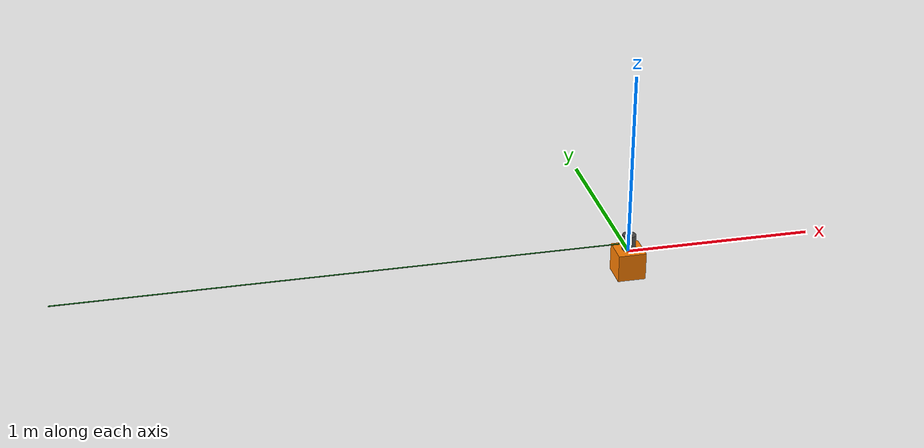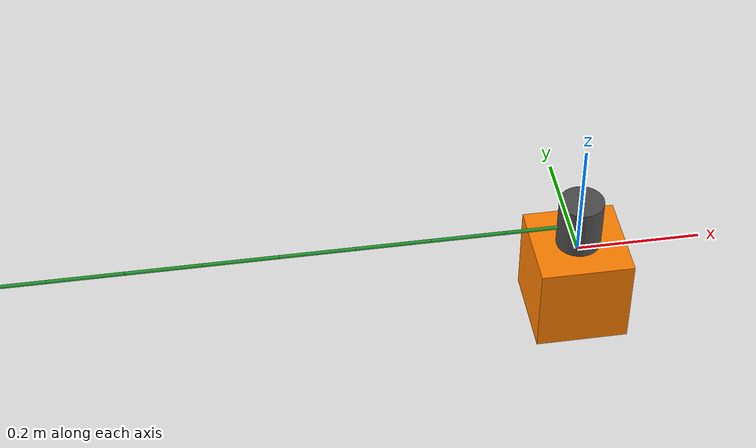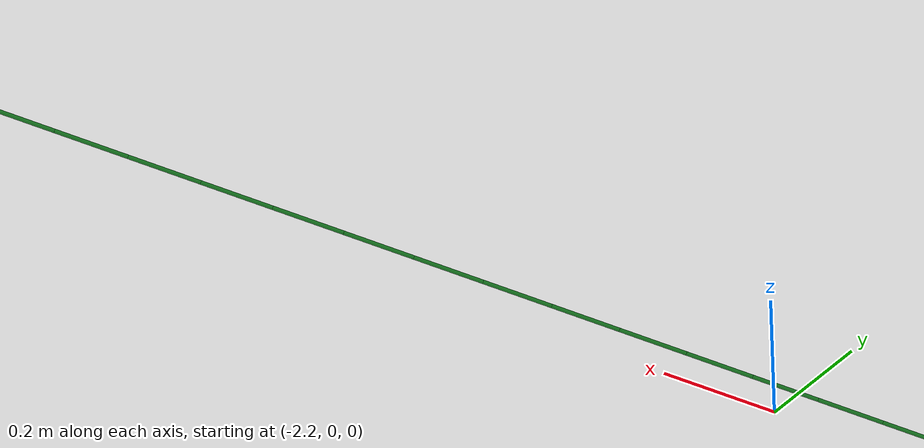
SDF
<?xml version="1.0" ?>
<!-- DO NOT EDIT: Generated from tether.sdf.jinja -->
<sdf version="1.9">
  <model name="tether">
    <pose>0.0 0.0 0.0 0.0 0.0 0.0</pose>
    <self_collide>false</self_collide>

    <link name="link_attachment">
      <gravity>true</gravity>
      <self_collide>false</self_collide>
      <pose>0.0 0.0 0.05 0.0 0 0.0</pose>
      <inertial>
        <mass>0.004</mass>
        <inertia>
          <ixx>4.233333333333333e-06</ixx>
          <ixy>0</ixy>
          <ixz>0</ixz>
          <iyy>4.233333333333333e-06</iyy>
          <iyz>0</iyz>
          <izz>1.8e-06</izz>
        </inertia>
      </inertial>
      <collision name="collision">
        <pose>0 0 0 0 0 0</pose>
        <geometry>
        <cylinder>
          <length>0.1</length>
          <radius>0.03</radius>
        </cylinder>
      </geometry>
        <surface>
          <contact>
            <ode>
              <min_depth>0.01</min_depth>        <!-- Đồng bộ với payload -->
              <max_vel>10.0</max_vel>            <!-- Đồng nhất với payload -->
              <kp>5e5</kp>                       <!-- Đồng nhất với payload và ground -->
              <kd>500</kd>                       <!-- Đồng nhất với payload và ground -->
            </ode>
          </contact>
          <friction>
            <ode>
              <mu>0.5</mu>
              <mu2>0.5</mu2>
            </ode>
          </friction>
        </surface>
        <max_contacts>4</max_contacts>
      </collision>
      <visual name="cylinder_visual">
        <geometry>
        <cylinder>
          <length>0.1</length>
          <radius>0.036</radius>
        </cylinder>
      </geometry>
        <material>
        <script>
          <name>Gazebo/DarkGray</name>
          <uri>file://media/materials/scripts/gazebo.material</uri>
        </script>
      </material>
      </visual>
    </link>

    <link name="link_0">
      <gravity>true</gravity>
      <self_collide>false</self_collide>
        <pose relative_to="link_attachment">-0.06 0 0 0 1.5707963267948966 0</pose>

      <inertial>
        <mass>0.005</mass>
        <inertia>
          <ixx>6.01125e-06</ixx>
          <ixy>0</ixy>
          <ixz>0</ixz>
          <iyy>6.01125e-06</iyy>
          <iyz>0</iyz>
          <izz>1e-06</izz>
        </inertia>
      </inertial><collision name="collision">
        <pose>0 0 0 0 0 0</pose>
        <geometry>
        <cylinder>
          <length>0.12</length>
          <radius>0.003</radius>
        </cylinder>
      </geometry>
        <surface>
          <contact>
            <ode>
              <min_depth>0.01</min_depth>        <!-- Đồng bộ với payload -->
              <max_vel>10.0</max_vel>            <!-- Đồng nhất với payload -->
              <kp>5e5</kp>                       <!-- Đồng nhất với payload và ground -->
              <kd>500</kd>                       <!-- Đồng nhất với payload và ground -->
            </ode>
          </contact>
          <friction>
            <ode>
              <mu>0.5</mu>
              <mu2>0.5</mu2>
            </ode>
          </friction>
        </surface>
        <max_contacts>4</max_contacts>
      </collision>
      <visual name="cylinder_visual">
        <geometry>
        <cylinder>
          <length>0.12</length>
          <radius>0.003</radius>
        </cylinder>
      </geometry>
        <material>
        <script>
          <name>Gazebo/Green</name>
          <uri>file://media/materials/scripts/gazebo.material</uri>
        </script>
      </material>
      </visual>
      <visual name="sphere_visual">
      <pose>0 0 0.06 0 0 0</pose>
        <geometry>
        <sphere>
          <radius>0.003</radius>
        </sphere>
      </geometry>
        <material>
        <script>
          <name>Gazebo/Green</name>
          <uri>file://media/materials/scripts/gazebo.material</uri>
        </script>
      </material>
      </visual>
    </link>

    <plugin filename="gz-sim-lift-drag-system" name="gz::sim::systems::LiftDrag">
      <a0>0</a0>
      <cla>0</cla>
      <cda>1.0</cda>
      <cma>0.0</cma>
      <alpha_stall>0</alpha_stall>
      <cla_stall>0</cla_stall>
      <cda_stall>1.4</cda_stall>
      <cma_stall>0.0</cma_stall>
      <cp>0 0 0</cp>
      <area>0.0007199999999999999</area>
      <air_density>1.225</air_density>
      <forward>0 1 0</forward>
      <upward>0 0 1</upward>
      <link_name>link_0</link_name>
    </plugin>
    <link name="link_1">
      <gravity>true</gravity>
      <self_collide>false</self_collide>

          <pose relative_to="link_0">0 0 -0.12 0 0 0</pose>

      <inertial>
        <mass>0.005</mass>
        <inertia>
          <ixx>6.01125e-06</ixx>
          <ixy>0</ixy>
          <ixz>0</ixz>
          <iyy>6.01125e-06</iyy>
          <iyz>0</iyz>
          <izz>1e-06</izz>
        </inertia>
      </inertial><collision name="collision">
        <pose>0 0 0 0 0 0</pose>
        <geometry>
        <cylinder>
          <length>0.12</length>
          <radius>0.003</radius>
        </cylinder>
      </geometry>
        <surface>
          <contact>
            <ode>
              <min_depth>0.01</min_depth>        <!-- Đồng bộ với payload -->
              <max_vel>10.0</max_vel>            <!-- Đồng nhất với payload -->
              <kp>5e5</kp>                       <!-- Đồng nhất với payload và ground -->
              <kd>500</kd>                       <!-- Đồng nhất với payload và ground -->
            </ode>
          </contact>
          <friction>
            <ode>
              <mu>0.5</mu>
              <mu2>0.5</mu2>
            </ode>
          </friction>
        </surface>
        <max_contacts>4</max_contacts>
      </collision>
      <visual name="cylinder_visual">
        <geometry>
        <cylinder>
          <length>0.12</length>
          <radius>0.003</radius>
        </cylinder>
      </geometry>
        <material>
        <script>
          <name>Gazebo/Green</name>
          <uri>file://media/materials/scripts/gazebo.material</uri>
        </script>
      </material>
      </visual>
      <visual name="sphere_visual">
      <pose>0 0 0.06 0 0 0</pose>
        <geometry>
        <sphere>
          <radius>0.003</radius>
        </sphere>
      </geometry>
        <material>
        <script>
          <name>Gazebo/Green</name>
          <uri>file://media/materials/scripts/gazebo.material</uri>
        </script>
      </material>
      </visual>
    </link>

    <plugin filename="gz-sim-lift-drag-system" name="gz::sim::systems::LiftDrag">
      <a0>0</a0>
      <cla>0</cla>
      <cda>1.0</cda>
      <cma>0.0</cma>
      <alpha_stall>0</alpha_stall>
      <cla_stall>0</cla_stall>
      <cda_stall>1.4</cda_stall>
      <cma_stall>0.0</cma_stall>
      <cp>0 0 0</cp>
      <area>0.0007199999999999999</area>
      <air_density>1.225</air_density>
      <forward>0 1 0</forward>
      <upward>0 0 1</upward>
      <link_name>link_1</link_name>
    </plugin>
    <link name="link_2">
      <gravity>true</gravity>
      <self_collide>false</self_collide>

          <pose relative_to="link_1">0 0 -0.12 0 0 0</pose>

      <inertial>
        <mass>0.005</mass>
        <inertia>
          <ixx>6.01125e-06</ixx>
          <ixy>0</ixy>
          <ixz>0</ixz>
          <iyy>6.01125e-06</iyy>
          <iyz>0</iyz>
          <izz>1e-06</izz>
        </inertia>
      </inertial><collision name="collision">
        <pose>0 0 0 0 0 0</pose>
        <geometry>
        <cylinder>
          <length>0.12</length>
          <radius>0.003</radius>
        </cylinder>
      </geometry>
        <surface>
          <contact>
            <ode>
              <min_depth>0.01</min_depth>        <!-- Đồng bộ với payload -->
              <max_vel>10.0</max_vel>            <!-- Đồng nhất với payload -->
              <kp>5e5</kp>                       <!-- Đồng nhất với payload và ground -->
              <kd>500</kd>                       <!-- Đồng nhất với payload và ground -->
            </ode>
          </contact>
          <friction>
            <ode>
              <mu>0.5</mu>
              <mu2>0.5</mu2>
            </ode>
          </friction>
        </surface>
        <max_contacts>4</max_contacts>
      </collision>
      <visual name="cylinder_visual">
        <geometry>
        <cylinder>
          <length>0.12</length>
          <radius>0.003</radius>
        </cylinder>
      </geometry>
        <material>
        <script>
          <name>Gazebo/Green</name>
          <uri>file://media/materials/scripts/gazebo.material</uri>
        </script>
      </material>
      </visual>
      <visual name="sphere_visual">
      <pose>0 0 0.06 0 0 0</pose>
        <geometry>
        <sphere>
          <radius>0.003</radius>
        </sphere>
      </geometry>
        <material>
        <script>
          <name>Gazebo/Green</name>
          <uri>file://media/materials/scripts/gazebo.material</uri>
        </script>
      </material>
      </visual>
    </link>

    <plugin filename="gz-sim-lift-drag-system" name="gz::sim::systems::LiftDrag">
      <a0>0</a0>
      <cla>0</cla>
      <cda>1.0</cda>
      <cma>0.0</cma>
      <alpha_stall>0</alpha_stall>
      <cla_stall>0</cla_stall>
      <cda_stall>1.4</cda_stall>
      <cma_stall>0.0</cma_stall>
      <cp>0 0 0</cp>
      <area>0.0007199999999999999</area>
      <air_density>1.225</air_density>
      <forward>0 1 0</forward>
      <upward>0 0 1</upward>
      <link_name>link_2</link_name>
    </plugin>
    <link name="link_3">
      <gravity>true</gravity>
      <self_collide>false</self_collide>
        <pose relative_to="link_2">0 0 -0.12 0 0 0</pose>

      <inertial>
        <mass>0.005</mass>
        <inertia>
          <ixx>6.01125e-06</ixx>
          <ixy>0</ixy>
          <ixz>0</ixz>
          <iyy>6.01125e-06</iyy>
          <iyz>0</iyz>
          <izz>1e-06</izz>
        </inertia>
      </inertial><collision name="collision">
        <pose>0 0 0 0 0 0</pose>
        <geometry>
        <cylinder>
          <length>0.12</length>
          <radius>0.003</radius>
        </cylinder>
      </geometry>
        <surface>
          <contact>
            <ode>
              <min_depth>0.01</min_depth>        <!-- Đồng bộ với payload -->
              <max_vel>10.0</max_vel>            <!-- Đồng nhất với payload -->
              <kp>5e5</kp>                       <!-- Đồng nhất với payload và ground -->
              <kd>500</kd>                       <!-- Đồng nhất với payload và ground -->
            </ode>
          </contact>
          <friction>
            <ode>
              <mu>0.5</mu>
              <mu2>0.5</mu2>
            </ode>
          </friction>
        </surface>
        <max_contacts>4</max_contacts>
      </collision>
      <visual name="cylinder_visual">
        <geometry>
        <cylinder>
          <length>0.12</length>
          <radius>0.003</radius>
        </cylinder>
      </geometry>
        <material>
        <script>
          <name>Gazebo/Green</name>
          <uri>file://media/materials/scripts/gazebo.material</uri>
        </script>
      </material>
      </visual>
      <visual name="sphere_visual">
      <pose>0 0 0.06 0 0 0</pose>
        <geometry>
        <sphere>
          <radius>0.003</radius>
        </sphere>
      </geometry>
        <material>
        <script>
          <name>Gazebo/Green</name>
          <uri>file://media/materials/scripts/gazebo.material</uri>
        </script>
      </material>
      </visual>
    </link>

    <plugin filename="gz-sim-lift-drag-system" name="gz::sim::systems::LiftDrag">
      <a0>0</a0>
      <cla>0</cla>
      <cda>1.0</cda>
      <cma>0.0</cma>
      <alpha_stall>0</alpha_stall>
      <cla_stall>0</cla_stall>
      <cda_stall>1.4</cda_stall>
      <cma_stall>0.0</cma_stall>
      <cp>0 0 0</cp>
      <area>0.0007199999999999999</area>
      <air_density>1.225</air_density>
      <forward>0 1 0</forward>
      <upward>0 0 1</upward>
      <link_name>link_3</link_name>
    </plugin>
    <link name="link_4">
      <gravity>true</gravity>
      <self_collide>false</self_collide>
        <pose relative_to="link_3">0 0 -0.12 0 0 0</pose>

      <inertial>
        <mass>0.005</mass>
        <inertia>
          <ixx>6.01125e-06</ixx>
          <ixy>0</ixy>
          <ixz>0</ixz>
          <iyy>6.01125e-06</iyy>
          <iyz>0</iyz>
          <izz>1e-06</izz>
        </inertia>
      </inertial><collision name="collision">
        <pose>0 0 0 0 0 0</pose>
        <geometry>
        <cylinder>
          <length>0.12</length>
          <radius>0.003</radius>
        </cylinder>
      </geometry>
        <surface>
          <contact>
            <ode>
              <min_depth>0.01</min_depth>        <!-- Đồng bộ với payload -->
              <max_vel>10.0</max_vel>            <!-- Đồng nhất với payload -->
              <kp>5e5</kp>                       <!-- Đồng nhất với payload và ground -->
              <kd>500</kd>                       <!-- Đồng nhất với payload và ground -->
            </ode>
          </contact>
          <friction>
            <ode>
              <mu>0.5</mu>
              <mu2>0.5</mu2>
            </ode>
          </friction>
        </surface>
        <max_contacts>4</max_contacts>
      </collision>
      <visual name="cylinder_visual">
        <geometry>
        <cylinder>
          <length>0.12</length>
          <radius>0.003</radius>
        </cylinder>
      </geometry>
        <material>
        <script>
          <name>Gazebo/Green</name>
          <uri>file://media/materials/scripts/gazebo.material</uri>
        </script>
      </material>
      </visual>
      <visual name="sphere_visual">
      <pose>0 0 0.06 0 0 0</pose>
        <geometry>
        <sphere>
          <radius>0.003</radius>
        </sphere>
      </geometry>
        <material>
        <script>
          <name>Gazebo/Green</name>
          <uri>file://media/materials/scripts/gazebo.material</uri>
        </script>
      </material>
      </visual>
    </link>

    <plugin filename="gz-sim-lift-drag-system" name="gz::sim::systems::LiftDrag">
      <a0>0</a0>
      <cla>0</cla>
      <cda>1.0</cda>
      <cma>0.0</cma>
      <alpha_stall>0</alpha_stall>
      <cla_stall>0</cla_stall>
      <cda_stall>1.4</cda_stall>
      <cma_stall>0.0</cma_stall>
      <cp>0 0 0</cp>
      <area>0.0007199999999999999</area>
      <air_density>1.225</air_density>
      <forward>0 1 0</forward>
      <upward>0 0 1</upward>
      <link_name>link_4</link_name>
    </plugin>
    <link name="link_5">
      <gravity>true</gravity>
      <self_collide>false</self_collide>
        <pose relative_to="link_4">0 0 -0.12 0 0 0</pose>

      <inertial>
        <mass>0.005</mass>
        <inertia>
          <ixx>6.01125e-06</ixx>
          <ixy>0</ixy>
          <ixz>0</ixz>
          <iyy>6.01125e-06</iyy>
          <iyz>0</iyz>
          <izz>1e-06</izz>
        </inertia>
      </inertial><collision name="collision">
        <pose>0 0 0 0 0 0</pose>
        <geometry>
        <cylinder>
          <length>0.12</length>
          <radius>0.003</radius>
        </cylinder>
      </geometry>
        <surface>
          <contact>
            <ode>
              <min_depth>0.01</min_depth>        <!-- Đồng bộ với payload -->
              <max_vel>10.0</max_vel>            <!-- Đồng nhất với payload -->
              <kp>5e5</kp>                       <!-- Đồng nhất với payload và ground -->
              <kd>500</kd>                       <!-- Đồng nhất với payload và ground -->
            </ode>
          </contact>
          <friction>
            <ode>
              <mu>0.5</mu>
              <mu2>0.5</mu2>
            </ode>
          </friction>
        </surface>
        <max_contacts>4</max_contacts>
      </collision>
      <visual name="cylinder_visual">
        <geometry>
        <cylinder>
          <length>0.12</length>
          <radius>0.003</radius>
        </cylinder>
      </geometry>
        <material>
        <script>
          <name>Gazebo/Green</name>
          <uri>file://media/materials/scripts/gazebo.material</uri>
        </script>
      </material>
      </visual>
      <visual name="sphere_visual">
      <pose>0 0 0.06 0 0 0</pose>
        <geometry>
        <sphere>
          <radius>0.003</radius>
        </sphere>
      </geometry>
        <material>
        <script>
          <name>Gazebo/Green</name>
          <uri>file://media/materials/scripts/gazebo.material</uri>
        </script>
      </material>
      </visual>
    </link>

    <plugin filename="gz-sim-lift-drag-system" name="gz::sim::systems::LiftDrag">
      <a0>0</a0>
      <cla>0</cla>
      <cda>1.0</cda>
      <cma>0.0</cma>
      <alpha_stall>0</alpha_stall>
      <cla_stall>0</cla_stall>
      <cda_stall>1.4</cda_stall>
      <cma_stall>0.0</cma_stall>
      <cp>0 0 0</cp>
      <area>0.0007199999999999999</area>
      <air_density>1.225</air_density>
      <forward>0 1 0</forward>
      <upward>0 0 1</upward>
      <link_name>link_5</link_name>
    </plugin>
    <link name="link_6">
      <gravity>true</gravity>
      <self_collide>false</self_collide>
        <pose relative_to="link_5">0 0 -0.12 0 0 0</pose>

      <inertial>
        <mass>0.005</mass>
        <inertia>
          <ixx>6.01125e-06</ixx>
          <ixy>0</ixy>
          <ixz>0</ixz>
          <iyy>6.01125e-06</iyy>
          <iyz>0</iyz>
          <izz>1e-06</izz>
        </inertia>
      </inertial><collision name="collision">
        <pose>0 0 0 0 0 0</pose>
        <geometry>
        <cylinder>
          <length>0.12</length>
          <radius>0.003</radius>
        </cylinder>
      </geometry>
        <surface>
          <contact>
            <ode>
              <min_depth>0.01</min_depth>        <!-- Đồng bộ với payload -->
              <max_vel>10.0</max_vel>            <!-- Đồng nhất với payload -->
              <kp>5e5</kp>                       <!-- Đồng nhất với payload và ground -->
              <kd>500</kd>                       <!-- Đồng nhất với payload và ground -->
            </ode>
          </contact>
          <friction>
            <ode>
              <mu>0.5</mu>
              <mu2>0.5</mu2>
            </ode>
          </friction>
        </surface>
        <max_contacts>4</max_contacts>
      </collision>
      <visual name="cylinder_visual">
        <geometry>
        <cylinder>
          <length>0.12</length>
          <radius>0.003</radius>
        </cylinder>
      </geometry>
        <material>
        <script>
          <name>Gazebo/Green</name>
          <uri>file://media/materials/scripts/gazebo.material</uri>
        </script>
      </material>
      </visual>
      <visual name="sphere_visual">
      <pose>0 0 0.06 0 0 0</pose>
        <geometry>
        <sphere>
          <radius>0.003</radius>
        </sphere>
      </geometry>
        <material>
        <script>
          <name>Gazebo/Green</name>
          <uri>file://media/materials/scripts/gazebo.material</uri>
        </script>
      </material>
      </visual>
    </link>

    <plugin filename="gz-sim-lift-drag-system" name="gz::sim::systems::LiftDrag">
      <a0>0</a0>
      <cla>0</cla>
      <cda>1.0</cda>
      <cma>0.0</cma>
      <alpha_stall>0</alpha_stall>
      <cla_stall>0</cla_stall>
      <cda_stall>1.4</cda_stall>
      <cma_stall>0.0</cma_stall>
      <cp>0 0 0</cp>
      <area>0.0007199999999999999</area>
      <air_density>1.225</air_density>
      <forward>0 1 0</forward>
      <upward>0 0 1</upward>
      <link_name>link_6</link_name>
    </plugin>
    <link name="link_7">
      <gravity>true</gravity>
      <self_collide>false</self_collide>
        <pose relative_to="link_6">0 0 -0.12 0 0 0</pose>

      <inertial>
        <mass>0.005</mass>
        <inertia>
          <ixx>6.01125e-06</ixx>
          <ixy>0</ixy>
          <ixz>0</ixz>
          <iyy>6.01125e-06</iyy>
          <iyz>0</iyz>
          <izz>1e-06</izz>
        </inertia>
      </inertial><collision name="collision">
        <pose>0 0 0 0 0 0</pose>
        <geometry>
        <cylinder>
          <length>0.12</length>
          <radius>0.003</radius>
        </cylinder>
      </geometry>
        <surface>
          <contact>
            <ode>
              <min_depth>0.01</min_depth>        <!-- Đồng bộ với payload -->
              <max_vel>10.0</max_vel>            <!-- Đồng nhất với payload -->
              <kp>5e5</kp>                       <!-- Đồng nhất với payload và ground -->
              <kd>500</kd>                       <!-- Đồng nhất với payload và ground -->
            </ode>
          </contact>
          <friction>
            <ode>
              <mu>0.5</mu>
              <mu2>0.5</mu2>
            </ode>
          </friction>
        </surface>
        <max_contacts>4</max_contacts>
      </collision>
      <visual name="cylinder_visual">
        <geometry>
        <cylinder>
          <length>0.12</length>
          <radius>0.003</radius>
        </cylinder>
      </geometry>
        <material>
        <script>
          <name>Gazebo/Green</name>
          <uri>file://media/materials/scripts/gazebo.material</uri>
        </script>
      </material>
      </visual>
      <visual name="sphere_visual">
      <pose>0 0 0.06 0 0 0</pose>
        <geometry>
        <sphere>
          <radius>0.003</radius>
        </sphere>
      </geometry>
        <material>
        <script>
          <name>Gazebo/Green</name>
          <uri>file://media/materials/scripts/gazebo.material</uri>
        </script>
      </material>
      </visual>
    </link>

    <plugin filename="gz-sim-lift-drag-system" name="gz::sim::systems::LiftDrag">
      <a0>0</a0>
      <cla>0</cla>
      <cda>1.0</cda>
      <cma>0.0</cma>
      <alpha_stall>0</alpha_stall>
      <cla_stall>0</cla_stall>
      <cda_stall>1.4</cda_stall>
      <cma_stall>0.0</cma_stall>
      <cp>0 0 0</cp>
      <area>0.0007199999999999999</area>
      <air_density>1.225</air_density>
      <forward>0 1 0</forward>
      <upward>0 0 1</upward>
      <link_name>link_7</link_name>
    </plugin>
    <link name="link_8">
      <gravity>true</gravity>
      <self_collide>false</self_collide>
        <pose relative_to="link_7">0 0 -0.12 0 0 0</pose>

      <inertial>
        <mass>0.005</mass>
        <inertia>
          <ixx>6.01125e-06</ixx>
          <ixy>0</ixy>
          <ixz>0</ixz>
          <iyy>6.01125e-06</iyy>
          <iyz>0</iyz>
          <izz>1e-06</izz>
        </inertia>
      </inertial><collision name="collision">
        <pose>0 0 0 0 0 0</pose>
        <geometry>
        <cylinder>
          <length>0.12</length>
          <radius>0.003</radius>
        </cylinder>
      </geometry>
        <surface>
          <contact>
            <ode>
              <min_depth>0.01</min_depth>        <!-- Đồng bộ với payload -->
              <max_vel>10.0</max_vel>            <!-- Đồng nhất với payload -->
              <kp>5e5</kp>                       <!-- Đồng nhất với payload và ground -->
              <kd>500</kd>                       <!-- Đồng nhất với payload và ground -->
            </ode>
          </contact>
          <friction>
            <ode>
              <mu>0.5</mu>
              <mu2>0.5</mu2>
            </ode>
          </friction>
        </surface>
        <max_contacts>4</max_contacts>
      </collision>
      <visual name="cylinder_visual">
        <geometry>
        <cylinder>
          <length>0.12</length>
          <radius>0.003</radius>
        </cylinder>
      </geometry>
        <material>
        <script>
          <name>Gazebo/Green</name>
          <uri>file://media/materials/scripts/gazebo.material</uri>
        </script>
      </material>
      </visual>
      <visual name="sphere_visual">
      <pose>0 0 0.06 0 0 0</pose>
        <geometry>
        <sphere>
          <radius>0.003</radius>
        </sphere>
      </geometry>
        <material>
        <script>
          <name>Gazebo/Green</name>
          <uri>file://media/materials/scripts/gazebo.material</uri>
        </script>
      </material>
      </visual>
    </link>

    <plugin filename="gz-sim-lift-drag-system" name="gz::sim::systems::LiftDrag">
      <a0>0</a0>
      <cla>0</cla>
      <cda>1.0</cda>
      <cma>0.0</cma>
      <alpha_stall>0</alpha_stall>
      <cla_stall>0</cla_stall>
      <cda_stall>1.4</cda_stall>
      <cma_stall>0.0</cma_stall>
      <cp>0 0 0</cp>
      <area>0.0007199999999999999</area>
      <air_density>1.225</air_density>
      <forward>0 1 0</forward>
      <upward>0 0 1</upward>
      <link_name>link_8</link_name>
    </plugin>
    <link name="link_9">
      <gravity>true</gravity>
      <self_collide>false</self_collide>
        <pose relative_to="link_8">0 0 -0.12 0 0 0</pose>

      <inertial>
        <mass>0.005</mass>
        <inertia>
          <ixx>6.01125e-06</ixx>
          <ixy>0</ixy>
          <ixz>0</ixz>
          <iyy>6.01125e-06</iyy>
          <iyz>0</iyz>
          <izz>1e-06</izz>
        </inertia>
      </inertial><collision name="collision">
        <pose>0 0 0 0 0 0</pose>
        <geometry>
        <cylinder>
          <length>0.12</length>
          <radius>0.003</radius>
        </cylinder>
      </geometry>
        <surface>
          <contact>
            <ode>
              <min_depth>0.01</min_depth>        <!-- Đồng bộ với payload -->
              <max_vel>10.0</max_vel>            <!-- Đồng nhất với payload -->
              <kp>5e5</kp>                       <!-- Đồng nhất với payload và ground -->
              <kd>500</kd>                       <!-- Đồng nhất với payload và ground -->
            </ode>
          </contact>
          <friction>
            <ode>
              <mu>0.5</mu>
              <mu2>0.5</mu2>
            </ode>
          </friction>
        </surface>
        <max_contacts>4</max_contacts>
      </collision>
      <visual name="cylinder_visual">
        <geometry>
        <cylinder>
          <length>0.12</length>
          <radius>0.003</radius>
        </cylinder>
      </geometry>
        <material>
        <script>
          <name>Gazebo/Green</name>
          <uri>file://media/materials/scripts/gazebo.material</uri>
        </script>
      </material>
      </visual>
      <visual name="sphere_visual">
      <pose>0 0 0.06 0 0 0</pose>
        <geometry>
        <sphere>
          <radius>0.003</radius>
        </sphere>
      </geometry>
        <material>
        <script>
          <name>Gazebo/Green</name>
          <uri>file://media/materials/scripts/gazebo.material</uri>
        </script>
      </material>
      </visual>
    </link>

    <plugin filename="gz-sim-lift-drag-system" name="gz::sim::systems::LiftDrag">
      <a0>0</a0>
      <cla>0</cla>
      <cda>1.0</cda>
      <cma>0.0</cma>
      <alpha_stall>0</alpha_stall>
      <cla_stall>0</cla_stall>
      <cda_stall>1.4</cda_stall>
      <cma_stall>0.0</cma_stall>
      <cp>0 0 0</cp>
      <area>0.0007199999999999999</area>
      <air_density>1.225</air_density>
      <forward>0 1 0</forward>
      <upward>0 0 1</upward>
      <link_name>link_9</link_name>
    </plugin>
    <link name="link_10">
      <gravity>true</gravity>
      <self_collide>false</self_collide>
        <pose relative_to="link_9">0 0 -0.12 0 0 0</pose>

      <inertial>
        <mass>0.005</mass>
        <inertia>
          <ixx>6.01125e-06</ixx>
          <ixy>0</ixy>
          <ixz>0</ixz>
          <iyy>6.01125e-06</iyy>
          <iyz>0</iyz>
          <izz>1e-06</izz>
        </inertia>
      </inertial><collision name="collision">
        <pose>0 0 0 0 0 0</pose>
        <geometry>
        <cylinder>
          <length>0.12</length>
          <radius>0.003</radius>
        </cylinder>
      </geometry>
        <surface>
          <contact>
            <ode>
              <min_depth>0.01</min_depth>        <!-- Đồng bộ với payload -->
              <max_vel>10.0</max_vel>            <!-- Đồng nhất với payload -->
              <kp>5e5</kp>                       <!-- Đồng nhất với payload và ground -->
              <kd>500</kd>                       <!-- Đồng nhất với payload và ground -->
            </ode>
          </contact>
          <friction>
            <ode>
              <mu>0.5</mu>
              <mu2>0.5</mu2>
            </ode>
          </friction>
        </surface>
        <max_contacts>4</max_contacts>
      </collision>
      <visual name="cylinder_visual">
        <geometry>
        <cylinder>
          <length>0.12</length>
          <radius>0.003</radius>
        </cylinder>
      </geometry>
        <material>
        <script>
          <name>Gazebo/Green</name>
          <uri>file://media/materials/scripts/gazebo.material</uri>
        </script>
      </material>
      </visual>
      <visual name="sphere_visual">
      <pose>0 0 0.06 0 0 0</pose>
        <geometry>
        <sphere>
          <radius>0.003</radius>
        </sphere>
      </geometry>
        <material>
        <script>
          <name>Gazebo/Green</name>
          <uri>file://media/materials/scripts/gazebo.material</uri>
        </script>
      </material>
      </visual>
    </link>

    <plugin filename="gz-sim-lift-drag-system" name="gz::sim::systems::LiftDrag">
      <a0>0</a0>
      <cla>0</cla>
      <cda>1.0</cda>
      <cma>0.0</cma>
      <alpha_stall>0</alpha_stall>
      <cla_stall>0</cla_stall>
      <cda_stall>1.4</cda_stall>
      <cma_stall>0.0</cma_stall>
      <cp>0 0 0</cp>
      <area>0.0007199999999999999</area>
      <air_density>1.225</air_density>
      <forward>0 1 0</forward>
      <upward>0 0 1</upward>
      <link_name>link_10</link_name>
    </plugin>
    <link name="link_11">
      <gravity>true</gravity>
      <self_collide>false</self_collide>
        <pose relative_to="link_10">0 0 -0.12 0 0 0</pose>

      <inertial>
        <mass>0.005</mass>
        <inertia>
          <ixx>6.01125e-06</ixx>
          <ixy>0</ixy>
          <ixz>0</ixz>
          <iyy>6.01125e-06</iyy>
          <iyz>0</iyz>
          <izz>1e-06</izz>
        </inertia>
      </inertial><collision name="collision">
        <pose>0 0 0 0 0 0</pose>
        <geometry>
        <cylinder>
          <length>0.12</length>
          <radius>0.003</radius>
        </cylinder>
      </geometry>
        <surface>
          <contact>
            <ode>
              <min_depth>0.01</min_depth>        <!-- Đồng bộ với payload -->
              <max_vel>10.0</max_vel>            <!-- Đồng nhất với payload -->
              <kp>5e5</kp>                       <!-- Đồng nhất với payload và ground -->
              <kd>500</kd>                       <!-- Đồng nhất với payload và ground -->
            </ode>
          </contact>
          <friction>
            <ode>
              <mu>0.5</mu>
              <mu2>0.5</mu2>
            </ode>
          </friction>
        </surface>
        <max_contacts>4</max_contacts>
      </collision>
      <visual name="cylinder_visual">
        <geometry>
        <cylinder>
          <length>0.12</length>
          <radius>0.003</radius>
        </cylinder>
      </geometry>
        <material>
        <script>
          <name>Gazebo/Green</name>
          <uri>file://media/materials/scripts/gazebo.material</uri>
        </script>
      </material>
      </visual>
      <visual name="sphere_visual">
      <pose>0 0 0.06 0 0 0</pose>
        <geometry>
        <sphere>
          <radius>0.003</radius>
        </sphere>
      </geometry>
        <material>
        <script>
          <name>Gazebo/Green</name>
          <uri>file://media/materials/scripts/gazebo.material</uri>
        </script>
      </material>
      </visual>
    </link>

    <plugin filename="gz-sim-lift-drag-system" name="gz::sim::systems::LiftDrag">
      <a0>0</a0>
      <cla>0</cla>
      <cda>1.0</cda>
      <cma>0.0</cma>
      <alpha_stall>0</alpha_stall>
      <cla_stall>0</cla_stall>
      <cda_stall>1.4</cda_stall>
      <cma_stall>0.0</cma_stall>
      <cp>0 0 0</cp>
      <area>0.0007199999999999999</area>
      <air_density>1.225</air_density>
      <forward>0 1 0</forward>
      <upward>0 0 1</upward>
      <link_name>link_11</link_name>
    </plugin>
    <link name="link_12">
      <gravity>true</gravity>
      <self_collide>false</self_collide>
        <pose relative_to="link_11">0 0 -0.12 0 0 0</pose>

      <inertial>
        <mass>0.005</mass>
        <inertia>
          <ixx>6.01125e-06</ixx>
          <ixy>0</ixy>
          <ixz>0</ixz>
          <iyy>6.01125e-06</iyy>
          <iyz>0</iyz>
          <izz>1e-06</izz>
        </inertia>
      </inertial><collision name="collision">
        <pose>0 0 0 0 0 0</pose>
        <geometry>
        <cylinder>
          <length>0.12</length>
          <radius>0.003</radius>
        </cylinder>
      </geometry>
        <surface>
          <contact>
            <ode>
              <min_depth>0.01</min_depth>        <!-- Đồng bộ với payload -->
              <max_vel>10.0</max_vel>            <!-- Đồng nhất với payload -->
              <kp>5e5</kp>                       <!-- Đồng nhất với payload và ground -->
              <kd>500</kd>                       <!-- Đồng nhất với payload và ground -->
            </ode>
          </contact>
          <friction>
            <ode>
              <mu>0.5</mu>
              <mu2>0.5</mu2>
            </ode>
          </friction>
        </surface>
        <max_contacts>4</max_contacts>
      </collision>
      <visual name="cylinder_visual">
        <geometry>
        <cylinder>
          <length>0.12</length>
          <radius>0.003</radius>
        </cylinder>
      </geometry>
        <material>
        <script>
          <name>Gazebo/Green</name>
          <uri>file://media/materials/scripts/gazebo.material</uri>
        </script>
      </material>
      </visual>
      <visual name="sphere_visual">
      <pose>0 0 0.06 0 0 0</pose>
        <geometry>
        <sphere>
          <radius>0.003</radius>
        </sphere>
      </geometry>
        <material>
        <script>
          <name>Gazebo/Green</name>
          <uri>file://media/materials/scripts/gazebo.material</uri>
        </script>
      </material>
      </visual>
    </link>

    <plugin filename="gz-sim-lift-drag-system" name="gz::sim::systems::LiftDrag">
      <a0>0</a0>
      <cla>0</cla>
      <cda>1.0</cda>
      <cma>0.0</cma>
      <alpha_stall>0</alpha_stall>
      <cla_stall>0</cla_stall>
      <cda_stall>1.4</cda_stall>
      <cma_stall>0.0</cma_stall>
      <cp>0 0 0</cp>
      <area>0.0007199999999999999</area>
      <air_density>1.225</air_density>
      <forward>0 1 0</forward>
      <upward>0 0 1</upward>
      <link_name>link_12</link_name>
    </plugin>
    <link name="link_13">
      <gravity>true</gravity>
      <self_collide>false</self_collide>
        <pose relative_to="link_12">0 0 -0.12 0 0 0</pose>

      <inertial>
        <mass>0.005</mass>
        <inertia>
          <ixx>6.01125e-06</ixx>
          <ixy>0</ixy>
          <ixz>0</ixz>
          <iyy>6.01125e-06</iyy>
          <iyz>0</iyz>
          <izz>1e-06</izz>
        </inertia>
      </inertial><collision name="collision">
        <pose>0 0 0 0 0 0</pose>
        <geometry>
        <cylinder>
          <length>0.12</length>
          <radius>0.003</radius>
        </cylinder>
      </geometry>
        <surface>
          <contact>
            <ode>
              <min_depth>0.01</min_depth>        <!-- Đồng bộ với payload -->
              <max_vel>10.0</max_vel>            <!-- Đồng nhất với payload -->
              <kp>5e5</kp>                       <!-- Đồng nhất với payload và ground -->
              <kd>500</kd>                       <!-- Đồng nhất với payload và ground -->
            </ode>
          </contact>
          <friction>
            <ode>
              <mu>0.5</mu>
              <mu2>0.5</mu2>
            </ode>
          </friction>
        </surface>
        <max_contacts>4</max_contacts>
      </collision>
      <visual name="cylinder_visual">
        <geometry>
        <cylinder>
          <length>0.12</length>
          <radius>0.003</radius>
        </cylinder>
      </geometry>
        <material>
        <script>
          <name>Gazebo/Green</name>
          <uri>file://media/materials/scripts/gazebo.material</uri>
        </script>
      </material>
      </visual>
      <visual name="sphere_visual">
      <pose>0 0 0.06 0 0 0</pose>
        <geometry>
        <sphere>
          <radius>0.003</radius>
        </sphere>
      </geometry>
        <material>
        <script>
          <name>Gazebo/Green</name>
          <uri>file://media/materials/scripts/gazebo.material</uri>
        </script>
      </material>
      </visual>
    </link>

    <plugin filename="gz-sim-lift-drag-system" name="gz::sim::systems::LiftDrag">
      <a0>0</a0>
      <cla>0</cla>
      <cda>1.0</cda>
      <cma>0.0</cma>
      <alpha_stall>0</alpha_stall>
      <cla_stall>0</cla_stall>
      <cda_stall>1.4</cda_stall>
      <cma_stall>0.0</cma_stall>
      <cp>0 0 0</cp>
      <area>0.0007199999999999999</area>
      <air_density>1.225</air_density>
      <forward>0 1 0</forward>
      <upward>0 0 1</upward>
      <link_name>link_13</link_name>
    </plugin>
    <link name="link_14">
      <gravity>true</gravity>
      <self_collide>false</self_collide>
        <pose relative_to="link_13">0 0 -0.12 0 0 0</pose>

      <inertial>
        <mass>0.005</mass>
        <inertia>
          <ixx>6.01125e-06</ixx>
          <ixy>0</ixy>
          <ixz>0</ixz>
          <iyy>6.01125e-06</iyy>
          <iyz>0</iyz>
          <izz>1e-06</izz>
        </inertia>
      </inertial><collision name="collision">
        <pose>0 0 0 0 0 0</pose>
        <geometry>
        <cylinder>
          <length>0.12</length>
          <radius>0.003</radius>
        </cylinder>
      </geometry>
        <surface>
          <contact>
            <ode>
              <min_depth>0.01</min_depth>        <!-- Đồng bộ với payload -->
              <max_vel>10.0</max_vel>            <!-- Đồng nhất với payload -->
              <kp>5e5</kp>                       <!-- Đồng nhất với payload và ground -->
              <kd>500</kd>                       <!-- Đồng nhất với payload và ground -->
            </ode>
          </contact>
          <friction>
            <ode>
              <mu>0.5</mu>
              <mu2>0.5</mu2>
            </ode>
          </friction>
        </surface>
        <max_contacts>4</max_contacts>
      </collision>
      <visual name="cylinder_visual">
        <geometry>
        <cylinder>
          <length>0.12</length>
          <radius>0.003</radius>
        </cylinder>
      </geometry>
        <material>
        <script>
          <name>Gazebo/Green</name>
          <uri>file://media/materials/scripts/gazebo.material</uri>
        </script>
      </material>
      </visual>
      <visual name="sphere_visual">
      <pose>0 0 0.06 0 0 0</pose>
        <geometry>
        <sphere>
          <radius>0.003</radius>
        </sphere>
      </geometry>
        <material>
        <script>
          <name>Gazebo/Green</name>
          <uri>file://media/materials/scripts/gazebo.material</uri>
        </script>
      </material>
      </visual>
    </link>

    <plugin filename="gz-sim-lift-drag-system" name="gz::sim::systems::LiftDrag">
      <a0>0</a0>
      <cla>0</cla>
      <cda>1.0</cda>
      <cma>0.0</cma>
      <alpha_stall>0</alpha_stall>
      <cla_stall>0</cla_stall>
      <cda_stall>1.4</cda_stall>
      <cma_stall>0.0</cma_stall>
      <cp>0 0 0</cp>
      <area>0.0007199999999999999</area>
      <air_density>1.225</air_density>
      <forward>0 1 0</forward>
      <upward>0 0 1</upward>
      <link_name>link_14</link_name>
    </plugin>
    <link name="link_15">
      <gravity>true</gravity>
      <self_collide>false</self_collide>
        <pose relative_to="link_14">0 0 -0.12 0 0 0</pose>

      <inertial>
        <mass>0.005</mass>
        <inertia>
          <ixx>6.01125e-06</ixx>
          <ixy>0</ixy>
          <ixz>0</ixz>
          <iyy>6.01125e-06</iyy>
          <iyz>0</iyz>
          <izz>1e-06</izz>
        </inertia>
      </inertial><collision name="collision">
        <pose>0 0 0 0 0 0</pose>
        <geometry>
        <cylinder>
          <length>0.12</length>
          <radius>0.003</radius>
        </cylinder>
      </geometry>
        <surface>
          <contact>
            <ode>
              <min_depth>0.01</min_depth>        <!-- Đồng bộ với payload -->
              <max_vel>10.0</max_vel>            <!-- Đồng nhất với payload -->
              <kp>5e5</kp>                       <!-- Đồng nhất với payload và ground -->
              <kd>500</kd>                       <!-- Đồng nhất với payload và ground -->
            </ode>
          </contact>
          <friction>
            <ode>
              <mu>0.5</mu>
              <mu2>0.5</mu2>
            </ode>
          </friction>
        </surface>
        <max_contacts>4</max_contacts>
      </collision>
      <visual name="cylinder_visual">
        <geometry>
        <cylinder>
          <length>0.12</length>
          <radius>0.003</radius>
        </cylinder>
      </geometry>
        <material>
        <script>
          <name>Gazebo/Green</name>
          <uri>file://media/materials/scripts/gazebo.material</uri>
        </script>
      </material>
      </visual>
      <visual name="sphere_visual">
      <pose>0 0 0.06 0 0 0</pose>
        <geometry>
        <sphere>
          <radius>0.003</radius>
        </sphere>
      </geometry>
        <material>
        <script>
          <name>Gazebo/Green</name>
          <uri>file://media/materials/scripts/gazebo.material</uri>
        </script>
      </material>
      </visual>
    </link>

    <plugin filename="gz-sim-lift-drag-system" name="gz::sim::systems::LiftDrag">
      <a0>0</a0>
      <cla>0</cla>
      <cda>1.0</cda>
      <cma>0.0</cma>
      <alpha_stall>0</alpha_stall>
      <cla_stall>0</cla_stall>
      <cda_stall>1.4</cda_stall>
      <cma_stall>0.0</cma_stall>
      <cp>0 0 0</cp>
      <area>0.0007199999999999999</area>
      <air_density>1.225</air_density>
      <forward>0 1 0</forward>
      <upward>0 0 1</upward>
      <link_name>link_15</link_name>
    </plugin>
    <link name="link_16">
      <gravity>true</gravity>
      <self_collide>false</self_collide>
        <pose relative_to="link_15">0 0 -0.12 0 0 0</pose>

      <inertial>
        <mass>0.005</mass>
        <inertia>
          <ixx>6.01125e-06</ixx>
          <ixy>0</ixy>
          <ixz>0</ixz>
          <iyy>6.01125e-06</iyy>
          <iyz>0</iyz>
          <izz>1e-06</izz>
        </inertia>
      </inertial><collision name="collision">
        <pose>0 0 0 0 0 0</pose>
        <geometry>
        <cylinder>
          <length>0.12</length>
          <radius>0.003</radius>
        </cylinder>
      </geometry>
        <surface>
          <contact>
            <ode>
              <min_depth>0.01</min_depth>        <!-- Đồng bộ với payload -->
              <max_vel>10.0</max_vel>            <!-- Đồng nhất với payload -->
              <kp>5e5</kp>                       <!-- Đồng nhất với payload và ground -->
              <kd>500</kd>                       <!-- Đồng nhất với payload và ground -->
            </ode>
          </contact>
          <friction>
            <ode>
              <mu>0.5</mu>
              <mu2>0.5</mu2>
            </ode>
          </friction>
        </surface>
        <max_contacts>4</max_contacts>
      </collision>
      <visual name="cylinder_visual">
        <geometry>
        <cylinder>
          <length>0.12</length>
          <radius>0.003</radius>
        </cylinder>
      </geometry>
        <material>
        <script>
          <name>Gazebo/Green</name>
          <uri>file://media/materials/scripts/gazebo.material</uri>
        </script>
      </material>
      </visual>
      <visual name="sphere_visual">
      <pose>0 0 0.06 0 0 0</pose>
        <geometry>
        <sphere>
          <radius>0.003</radius>
        </sphere>
      </geometry>
        <material>
        <script>
          <name>Gazebo/Green</name>
          <uri>file://media/materials/scripts/gazebo.material</uri>
        </script>
      </material>
      </visual>
    </link>

    <plugin filename="gz-sim-lift-drag-system" name="gz::sim::systems::LiftDrag">
      <a0>0</a0>
      <cla>0</cla>
      <cda>1.0</cda>
      <cma>0.0</cma>
      <alpha_stall>0</alpha_stall>
      <cla_stall>0</cla_stall>
      <cda_stall>1.4</cda_stall>
      <cma_stall>0.0</cma_stall>
      <cp>0 0 0</cp>
      <area>0.0007199999999999999</area>
      <air_density>1.225</air_density>
      <forward>0 1 0</forward>
      <upward>0 0 1</upward>
      <link_name>link_16</link_name>
    </plugin>
    <link name="link_17">
      <gravity>true</gravity>
      <self_collide>false</self_collide>
        <pose relative_to="link_16">0 0 -0.12 0 0 0</pose>

      <inertial>
        <mass>0.005</mass>
        <inertia>
          <ixx>6.01125e-06</ixx>
          <ixy>0</ixy>
          <ixz>0</ixz>
          <iyy>6.01125e-06</iyy>
          <iyz>0</iyz>
          <izz>1e-06</izz>
        </inertia>
      </inertial><collision name="collision">
        <pose>0 0 0 0 0 0</pose>
        <geometry>
        <cylinder>
          <length>0.12</length>
          <radius>0.003</radius>
        </cylinder>
      </geometry>
        <surface>
          <contact>
            <ode>
              <min_depth>0.01</min_depth>        <!-- Đồng bộ với payload -->
              <max_vel>10.0</max_vel>            <!-- Đồng nhất với payload -->
              <kp>5e5</kp>                       <!-- Đồng nhất với payload và ground -->
              <kd>500</kd>                       <!-- Đồng nhất với payload và ground -->
            </ode>
          </contact>
          <friction>
            <ode>
              <mu>0.5</mu>
              <mu2>0.5</mu2>
            </ode>
          </friction>
        </surface>
        <max_contacts>4</max_contacts>
      </collision>
      <visual name="cylinder_visual">
        <geometry>
        <cylinder>
          <length>0.12</length>
          <radius>0.003</radius>
        </cylinder>
      </geometry>
        <material>
        <script>
          <name>Gazebo/Green</name>
          <uri>file://media/materials/scripts/gazebo.material</uri>
        </script>
      </material>
      </visual>
      <visual name="sphere_visual">
      <pose>0 0 0.06 0 0 0</pose>
        <geometry>
        <sphere>
          <radius>0.003</radius>
        </sphere>
      </geometry>
        <material>
        <script>
          <name>Gazebo/Green</name>
          <uri>file://media/materials/scripts/gazebo.material</uri>
        </script>
      </material>
      </visual>
    </link>

    <plugin filename="gz-sim-lift-drag-system" name="gz::sim::systems::LiftDrag">
      <a0>0</a0>
      <cla>0</cla>
      <cda>1.0</cda>
      <cma>0.0</cma>
      <alpha_stall>0</alpha_stall>
      <cla_stall>0</cla_stall>
      <cda_stall>1.4</cda_stall>
      <cma_stall>0.0</cma_stall>
      <cp>0 0 0</cp>
      <area>0.0007199999999999999</area>
      <air_density>1.225</air_density>
      <forward>0 1 0</forward>
      <upward>0 0 1</upward>
      <link_name>link_17</link_name>
    </plugin>
    <link name="link_18">
      <gravity>true</gravity>
      <self_collide>false</self_collide>
        <pose relative_to="link_17">0 0 -0.12 0 0 0</pose>

      <inertial>
        <mass>0.005</mass>
        <inertia>
          <ixx>6.01125e-06</ixx>
          <ixy>0</ixy>
          <ixz>0</ixz>
          <iyy>6.01125e-06</iyy>
          <iyz>0</iyz>
          <izz>1e-06</izz>
        </inertia>
      </inertial><collision name="collision">
        <pose>0 0 0 0 0 0</pose>
        <geometry>
        <cylinder>
          <length>0.12</length>
          <radius>0.003</radius>
        </cylinder>
      </geometry>
        <surface>
          <contact>
            <ode>
              <min_depth>0.01</min_depth>        <!-- Đồng bộ với payload -->
              <max_vel>10.0</max_vel>            <!-- Đồng nhất với payload -->
              <kp>5e5</kp>                       <!-- Đồng nhất với payload và ground -->
              <kd>500</kd>                       <!-- Đồng nhất với payload và ground -->
            </ode>
          </contact>
          <friction>
            <ode>
              <mu>0.5</mu>
              <mu2>0.5</mu2>
            </ode>
          </friction>
        </surface>
        <max_contacts>4</max_contacts>
      </collision>
      <visual name="cylinder_visual">
        <geometry>
        <cylinder>
          <length>0.12</length>
          <radius>0.003</radius>
        </cylinder>
      </geometry>
        <material>
        <script>
          <name>Gazebo/Green</name>
          <uri>file://media/materials/scripts/gazebo.material</uri>
        </script>
      </material>
      </visual>
      <visual name="sphere_visual">
      <pose>0 0 0.06 0 0 0</pose>
        <geometry>
        <sphere>
          <radius>0.003</radius>
        </sphere>
      </geometry>
        <material>
        <script>
          <name>Gazebo/Green</name>
          <uri>file://media/materials/scripts/gazebo.material</uri>
        </script>
      </material>
      </visual>
    </link>

    <plugin filename="gz-sim-lift-drag-system" name="gz::sim::systems::LiftDrag">
      <a0>0</a0>
      <cla>0</cla>
      <cda>1.0</cda>
      <cma>0.0</cma>
      <alpha_stall>0</alpha_stall>
      <cla_stall>0</cla_stall>
      <cda_stall>1.4</cda_stall>
      <cma_stall>0.0</cma_stall>
      <cp>0 0 0</cp>
      <area>0.0007199999999999999</area>
      <air_density>1.225</air_density>
      <forward>0 1 0</forward>
      <upward>0 0 1</upward>
      <link_name>link_18</link_name>
    </plugin>
    <link name="link_19">
      <gravity>true</gravity>
      <self_collide>false</self_collide>
        <pose relative_to="link_18">0 0 -0.12 0 0 0</pose>

      <inertial>
        <mass>0.005</mass>
        <inertia>
          <ixx>6.01125e-06</ixx>
          <ixy>0</ixy>
          <ixz>0</ixz>
          <iyy>6.01125e-06</iyy>
          <iyz>0</iyz>
          <izz>1e-06</izz>
        </inertia>
      </inertial><collision name="collision">
        <pose>0 0 0 0 0 0</pose>
        <geometry>
        <cylinder>
          <length>0.12</length>
          <radius>0.003</radius>
        </cylinder>
      </geometry>
        <surface>
          <contact>
            <ode>
              <min_depth>0.01</min_depth>        <!-- Đồng bộ với payload -->
              <max_vel>10.0</max_vel>            <!-- Đồng nhất với payload -->
              <kp>5e5</kp>                       <!-- Đồng nhất với payload và ground -->
              <kd>500</kd>                       <!-- Đồng nhất với payload và ground -->
            </ode>
          </contact>
          <friction>
            <ode>
              <mu>0.5</mu>
              <mu2>0.5</mu2>
            </ode>
          </friction>
        </surface>
        <max_contacts>4</max_contacts>
      </collision>
      <visual name="cylinder_visual">
        <geometry>
        <cylinder>
          <length>0.12</length>
          <radius>0.003</radius>
        </cylinder>
      </geometry>
        <material>
        <script>
          <name>Gazebo/Green</name>
          <uri>file://media/materials/scripts/gazebo.material</uri>
        </script>
      </material>
      </visual>
      <visual name="sphere_visual">
      <pose>0 0 0.06 0 0 0</pose>
        <geometry>
        <sphere>
          <radius>0.003</radius>
        </sphere>
      </geometry>
        <material>
        <script>
          <name>Gazebo/Green</name>
          <uri>file://media/materials/scripts/gazebo.material</uri>
        </script>
      </material>
      </visual>
    </link>

    <plugin filename="gz-sim-lift-drag-system" name="gz::sim::systems::LiftDrag">
      <a0>0</a0>
      <cla>0</cla>
      <cda>1.0</cda>
      <cma>0.0</cma>
      <alpha_stall>0</alpha_stall>
      <cla_stall>0</cla_stall>
      <cda_stall>1.4</cda_stall>
      <cma_stall>0.0</cma_stall>
      <cp>0 0 0</cp>
      <area>0.0007199999999999999</area>
      <air_density>1.225</air_density>
      <forward>0 1 0</forward>
      <upward>0 0 1</upward>
      <link_name>link_19</link_name>
    </plugin>
    <link name="link_20">
      <gravity>true</gravity>
      <self_collide>false</self_collide>
        <pose relative_to="link_19">0 0 -0.12 0 0 0</pose>

      <inertial>
        <mass>0.005</mass>
        <inertia>
          <ixx>6.01125e-06</ixx>
          <ixy>0</ixy>
          <ixz>0</ixz>
          <iyy>6.01125e-06</iyy>
          <iyz>0</iyz>
          <izz>1e-06</izz>
        </inertia>
      </inertial><collision name="collision">
        <pose>0 0 0 0 0 0</pose>
        <geometry>
        <cylinder>
          <length>0.12</length>
          <radius>0.003</radius>
        </cylinder>
      </geometry>
        <surface>
          <contact>
            <ode>
              <min_depth>0.01</min_depth>        <!-- Đồng bộ với payload -->
              <max_vel>10.0</max_vel>            <!-- Đồng nhất với payload -->
              <kp>5e5</kp>                       <!-- Đồng nhất với payload và ground -->
              <kd>500</kd>                       <!-- Đồng nhất với payload và ground -->
            </ode>
          </contact>
          <friction>
            <ode>
              <mu>0.5</mu>
              <mu2>0.5</mu2>
            </ode>
          </friction>
        </surface>
        <max_contacts>4</max_contacts>
      </collision>
      <visual name="cylinder_visual">
        <geometry>
        <cylinder>
          <length>0.12</length>
          <radius>0.003</radius>
        </cylinder>
      </geometry>
        <material>
        <script>
          <name>Gazebo/Green</name>
          <uri>file://media/materials/scripts/gazebo.material</uri>
        </script>
      </material>
      </visual>
      <visual name="sphere_visual">
      <pose>0 0 0.06 0 0 0</pose>
        <geometry>
        <sphere>
          <radius>0.003</radius>
        </sphere>
      </geometry>
        <material>
        <script>
          <name>Gazebo/Green</name>
          <uri>file://media/materials/scripts/gazebo.material</uri>
        </script>
      </material>
      </visual>
    </link>

    <plugin filename="gz-sim-lift-drag-system" name="gz::sim::systems::LiftDrag">
      <a0>0</a0>
      <cla>0</cla>
      <cda>1.0</cda>
      <cma>0.0</cma>
      <alpha_stall>0</alpha_stall>
      <cla_stall>0</cla_stall>
      <cda_stall>1.4</cda_stall>
      <cma_stall>0.0</cma_stall>
      <cp>0 0 0</cp>
      <area>0.0007199999999999999</area>
      <air_density>1.225</air_density>
      <forward>0 1 0</forward>
      <upward>0 0 1</upward>
      <link_name>link_20</link_name>
    </plugin>
    <link name="link_21">
      <gravity>true</gravity>
      <self_collide>false</self_collide>
        <pose relative_to="link_20">0 0 -0.12 0 0 0</pose>

      <inertial>
        <mass>0.005</mass>
        <inertia>
          <ixx>6.01125e-06</ixx>
          <ixy>0</ixy>
          <ixz>0</ixz>
          <iyy>6.01125e-06</iyy>
          <iyz>0</iyz>
          <izz>1e-06</izz>
        </inertia>
      </inertial><collision name="collision">
        <pose>0 0 0 0 0 0</pose>
        <geometry>
        <cylinder>
          <length>0.12</length>
          <radius>0.003</radius>
        </cylinder>
      </geometry>
        <surface>
          <contact>
            <ode>
              <min_depth>0.01</min_depth>        <!-- Đồng bộ với payload -->
              <max_vel>10.0</max_vel>            <!-- Đồng nhất với payload -->
              <kp>5e5</kp>                       <!-- Đồng nhất với payload và ground -->
              <kd>500</kd>                       <!-- Đồng nhất với payload và ground -->
            </ode>
          </contact>
          <friction>
            <ode>
              <mu>0.5</mu>
              <mu2>0.5</mu2>
            </ode>
          </friction>
        </surface>
        <max_contacts>4</max_contacts>
      </collision>
      <visual name="cylinder_visual">
        <geometry>
        <cylinder>
          <length>0.12</length>
          <radius>0.003</radius>
        </cylinder>
      </geometry>
        <material>
        <script>
          <name>Gazebo/Green</name>
          <uri>file://media/materials/scripts/gazebo.material</uri>
        </script>
      </material>
      </visual>
      <visual name="sphere_visual">
      <pose>0 0 0.06 0 0 0</pose>
        <geometry>
        <sphere>
          <radius>0.003</radius>
        </sphere>
      </geometry>
        <material>
        <script>
          <name>Gazebo/Green</name>
          <uri>file://media/materials/scripts/gazebo.material</uri>
        </script>
      </material>
      </visual>
    </link>

    <plugin filename="gz-sim-lift-drag-system" name="gz::sim::systems::LiftDrag">
      <a0>0</a0>
      <cla>0</cla>
      <cda>1.0</cda>
      <cma>0.0</cma>
      <alpha_stall>0</alpha_stall>
      <cla_stall>0</cla_stall>
      <cda_stall>1.4</cda_stall>
      <cma_stall>0.0</cma_stall>
      <cp>0 0 0</cp>
      <area>0.0007199999999999999</area>
      <air_density>1.225</air_density>
      <forward>0 1 0</forward>
      <upward>0 0 1</upward>
      <link_name>link_21</link_name>
    </plugin>
    <link name="link_22">
      <gravity>true</gravity>
      <self_collide>false</self_collide>
        <pose relative_to="link_21">0 0 -0.12 0 0 0</pose>

      <inertial>
        <mass>0.005</mass>
        <inertia>
          <ixx>6.01125e-06</ixx>
          <ixy>0</ixy>
          <ixz>0</ixz>
          <iyy>6.01125e-06</iyy>
          <iyz>0</iyz>
          <izz>1e-06</izz>
        </inertia>
      </inertial><collision name="collision">
        <pose>0 0 0 0 0 0</pose>
        <geometry>
        <cylinder>
          <length>0.12</length>
          <radius>0.003</radius>
        </cylinder>
      </geometry>
        <surface>
          <contact>
            <ode>
              <min_depth>0.01</min_depth>        <!-- Đồng bộ với payload -->
              <max_vel>10.0</max_vel>            <!-- Đồng nhất với payload -->
              <kp>5e5</kp>                       <!-- Đồng nhất với payload và ground -->
              <kd>500</kd>                       <!-- Đồng nhất với payload và ground -->
            </ode>
          </contact>
          <friction>
            <ode>
              <mu>0.5</mu>
              <mu2>0.5</mu2>
            </ode>
          </friction>
        </surface>
        <max_contacts>4</max_contacts>
      </collision>
      <visual name="cylinder_visual">
        <geometry>
        <cylinder>
          <length>0.12</length>
          <radius>0.003</radius>
        </cylinder>
      </geometry>
        <material>
        <script>
          <name>Gazebo/Green</name>
          <uri>file://media/materials/scripts/gazebo.material</uri>
        </script>
      </material>
      </visual>
      <visual name="sphere_visual">
      <pose>0 0 0.06 0 0 0</pose>
        <geometry>
        <sphere>
          <radius>0.003</radius>
        </sphere>
      </geometry>
        <material>
        <script>
          <name>Gazebo/Green</name>
          <uri>file://media/materials/scripts/gazebo.material</uri>
        </script>
      </material>
      </visual>
    </link>

    <plugin filename="gz-sim-lift-drag-system" name="gz::sim::systems::LiftDrag">
      <a0>0</a0>
      <cla>0</cla>
      <cda>1.0</cda>
      <cma>0.0</cma>
      <alpha_stall>0</alpha_stall>
      <cla_stall>0</cla_stall>
      <cda_stall>1.4</cda_stall>
      <cma_stall>0.0</cma_stall>
      <cp>0 0 0</cp>
      <area>0.0007199999999999999</area>
      <air_density>1.225</air_density>
      <forward>0 1 0</forward>
      <upward>0 0 1</upward>
      <link_name>link_22</link_name>
    </plugin>
    <link name="link_23">
      <gravity>true</gravity>
      <self_collide>false</self_collide>
        <pose relative_to="link_22">0 0 -0.12 0 0 0</pose>

      <inertial>
        <mass>0.005</mass>
        <inertia>
          <ixx>6.01125e-06</ixx>
          <ixy>0</ixy>
          <ixz>0</ixz>
          <iyy>6.01125e-06</iyy>
          <iyz>0</iyz>
          <izz>1e-06</izz>
        </inertia>
      </inertial><collision name="collision">
        <pose>0 0 0 0 0 0</pose>
        <geometry>
        <cylinder>
          <length>0.12</length>
          <radius>0.003</radius>
        </cylinder>
      </geometry>
        <surface>
          <contact>
            <ode>
              <min_depth>0.01</min_depth>        <!-- Đồng bộ với payload -->
              <max_vel>10.0</max_vel>            <!-- Đồng nhất với payload -->
              <kp>5e5</kp>                       <!-- Đồng nhất với payload và ground -->
              <kd>500</kd>                       <!-- Đồng nhất với payload và ground -->
            </ode>
          </contact>
          <friction>
            <ode>
              <mu>0.5</mu>
              <mu2>0.5</mu2>
            </ode>
          </friction>
        </surface>
        <max_contacts>4</max_contacts>
      </collision>
      <visual name="cylinder_visual">
        <geometry>
        <cylinder>
          <length>0.12</length>
          <radius>0.003</radius>
        </cylinder>
      </geometry>
        <material>
        <script>
          <name>Gazebo/Green</name>
          <uri>file://media/materials/scripts/gazebo.material</uri>
        </script>
      </material>
      </visual>
      <visual name="sphere_visual">
      <pose>0 0 0.06 0 0 0</pose>
        <geometry>
        <sphere>
          <radius>0.003</radius>
        </sphere>
      </geometry>
        <material>
        <script>
          <name>Gazebo/Green</name>
          <uri>file://media/materials/scripts/gazebo.material</uri>
        </script>
      </material>
      </visual>
    </link>

    <plugin filename="gz-sim-lift-drag-system" name="gz::sim::systems::LiftDrag">
      <a0>0</a0>
      <cla>0</cla>
      <cda>1.0</cda>
      <cma>0.0</cma>
      <alpha_stall>0</alpha_stall>
      <cla_stall>0</cla_stall>
      <cda_stall>1.4</cda_stall>
      <cma_stall>0.0</cma_stall>
      <cp>0 0 0</cp>
      <area>0.0007199999999999999</area>
      <air_density>1.225</air_density>
      <forward>0 1 0</forward>
      <upward>0 0 1</upward>
      <link_name>link_23</link_name>
    </plugin>
    <link name="link_24">
      <gravity>true</gravity>
      <self_collide>false</self_collide>
        <pose relative_to="link_23">0 0 -0.12 0 0 0</pose>

      <inertial>
        <mass>0.005</mass>
        <inertia>
          <ixx>6.01125e-06</ixx>
          <ixy>0</ixy>
          <ixz>0</ixz>
          <iyy>6.01125e-06</iyy>
          <iyz>0</iyz>
          <izz>1e-06</izz>
        </inertia>
      </inertial><collision name="collision">
        <pose>0 0 0 0 0 0</pose>
        <geometry>
        <cylinder>
          <length>0.12</length>
          <radius>0.003</radius>
        </cylinder>
      </geometry>
        <surface>
          <contact>
            <ode>
              <min_depth>0.01</min_depth>        <!-- Đồng bộ với payload -->
              <max_vel>10.0</max_vel>            <!-- Đồng nhất với payload -->
              <kp>5e5</kp>                       <!-- Đồng nhất với payload và ground -->
              <kd>500</kd>                       <!-- Đồng nhất với payload và ground -->
            </ode>
          </contact>
          <friction>
            <ode>
              <mu>0.5</mu>
              <mu2>0.5</mu2>
            </ode>
          </friction>
        </surface>
        <max_contacts>4</max_contacts>
      </collision>
      <visual name="cylinder_visual">
        <geometry>
        <cylinder>
          <length>0.12</length>
          <radius>0.003</radius>
        </cylinder>
      </geometry>
        <material>
        <script>
          <name>Gazebo/Green</name>
          <uri>file://media/materials/scripts/gazebo.material</uri>
        </script>
      </material>
      </visual>
      <visual name="sphere_visual">
      <pose>0 0 0.06 0 0 0</pose>
        <geometry>
        <sphere>
          <radius>0.003</radius>
        </sphere>
      </geometry>
        <material>
        <script>
          <name>Gazebo/Green</name>
          <uri>file://media/materials/scripts/gazebo.material</uri>
        </script>
      </material>
      </visual>
    </link>

    <plugin filename="gz-sim-lift-drag-system" name="gz::sim::systems::LiftDrag">
      <a0>0</a0>
      <cla>0</cla>
      <cda>1.0</cda>
      <cma>0.0</cma>
      <alpha_stall>0</alpha_stall>
      <cla_stall>0</cla_stall>
      <cda_stall>1.4</cda_stall>
      <cma_stall>0.0</cma_stall>
      <cp>0 0 0</cp>
      <area>0.0007199999999999999</area>
      <air_density>1.225</air_density>
      <forward>0 1 0</forward>
      <upward>0 0 1</upward>
      <link_name>link_24</link_name>
    </plugin>

      <joint name="joint_0" type="ball">
      <parent>link_attachment</parent>
      <child>link_0</child>
      <pose>0 0 0.06 0 0 0</pose>
      <axis>
        <limit>
          <effort>4500</effort>
          <velocity>50</velocity>
        </limit>
        <dynamics>
          <damping>0.02</damping>
          <friction>0.005</friction>
          <spring_stiffness>0</spring_stiffness>
          <spring_reference>0.0</spring_reference>
        </dynamics>
        <!-- Ball joint không cần định nghĩa xyz vì rotate tự do 3 trục -->
      </axis>
      <physics>
        <ode>
          <cfm>0.001</cfm>
          <erp>0.4</erp>
        </ode>
      </physics>
    </joint>

        <joint name="joint_1" type="universal">
      <parent>link_0</parent>
      <child>link_1</child>
      <pose relative_to="link_1">0 0 0.06 0 0 0</pose>
      <axis>
        <xyz expressed_in="__model__">1 0 0</xyz>
        <limit>
          <lower>-6.14159</lower>
          <upper>6.14159</upper>
          <effort>4500</effort>
          <velocity>50</velocity>
        </limit>
        <dynamics>
          <damping>0.02</damping>
          <friction>0.005</friction>
          <spring_stiffness>0</spring_stiffness>
          <spring_reference>0.0</spring_reference>
        </dynamics>
      </axis>
      <axis2>
        <xyz expressed_in="__model__">0 1 0</xyz>
        <limit>
          <lower>-6.14159</lower>
          <upper>6.14159</upper>
          <effort>4500</effort>
          <velocity>50</velocity>
        </limit>
        <dynamics>
          <damping>0.02</damping>
          <friction>0.005</friction>
          <spring_stiffness>0</spring_stiffness>
          <spring_reference>0.0</spring_reference>
        </dynamics>
      </axis2>
      <physics>
        <ode>
          <cfm>0.001</cfm>
          <erp>0.4</erp>
        </ode>
      </physics>
    </joint>

        <joint name="joint_2" type="universal">
      <parent>link_1</parent>
      <child>link_2</child>
      <pose relative_to="link_2">0 0 0.06 0 0 0</pose>
      <axis>
        <xyz expressed_in="__model__">1 0 0</xyz>
        <limit>
          <lower>-6.14159</lower>
          <upper>6.14159</upper>
          <effort>4500</effort>
          <velocity>50</velocity>
        </limit>
        <dynamics>
          <damping>0.02</damping>
          <friction>0.005</friction>
          <spring_stiffness>0</spring_stiffness>
          <spring_reference>0.0</spring_reference>
        </dynamics>
      </axis>
      <axis2>
        <xyz expressed_in="__model__">0 1 0</xyz>
        <limit>
          <lower>-6.14159</lower>
          <upper>6.14159</upper>
          <effort>4500</effort>
          <velocity>50</velocity>
        </limit>
        <dynamics>
          <damping>0.02</damping>
          <friction>0.005</friction>
          <spring_stiffness>0</spring_stiffness>
          <spring_reference>0.0</spring_reference>
        </dynamics>
      </axis2>
      <physics>
        <ode>
          <cfm>0.001</cfm>
          <erp>0.4</erp>
        </ode>
      </physics>
    </joint>

        <joint name="joint_3" type="universal">
      <parent>link_2</parent>
      <child>link_3</child>
      <pose relative_to="link_3">0 0 0.06 0 0 0</pose>
      <axis>
        <xyz expressed_in="__model__">1 0 0</xyz>
        <limit>
          <lower>-6.14159</lower>
          <upper>6.14159</upper>
          <effort>4500</effort>
          <velocity>50</velocity>
        </limit>
        <dynamics>
          <damping>0.02</damping>
          <friction>0.005</friction>
          <spring_stiffness>0</spring_stiffness>
          <spring_reference>0.0</spring_reference>
        </dynamics>
      </axis>
      <axis2>
        <xyz expressed_in="__model__">0 1 0</xyz>
        <limit>
          <lower>-6.14159</lower>
          <upper>6.14159</upper>
          <effort>4500</effort>
          <velocity>50</velocity>
        </limit>
        <dynamics>
          <damping>0.02</damping>
          <friction>0.005</friction>
          <spring_stiffness>0</spring_stiffness>
          <spring_reference>0.0</spring_reference>
        </dynamics>
      </axis2>
      <physics>
        <ode>
          <cfm>0.001</cfm>
          <erp>0.4</erp>
        </ode>
      </physics>
    </joint>

        <joint name="joint_4" type="universal">
      <parent>link_3</parent>
      <child>link_4</child>
      <pose relative_to="link_4">0 0 0.06 0 0 0</pose>
      <axis>
        <xyz expressed_in="__model__">1 0 0</xyz>
        <limit>
          <lower>-6.14159</lower>
          <upper>6.14159</upper>
          <effort>4500</effort>
          <velocity>50</velocity>
        </limit>
        <dynamics>
          <damping>0.02</damping>
          <friction>0.005</friction>
          <spring_stiffness>0</spring_stiffness>
          <spring_reference>0.0</spring_reference>
        </dynamics>
      </axis>
      <axis2>
        <xyz expressed_in="__model__">0 1 0</xyz>
        <limit>
          <lower>-6.14159</lower>
          <upper>6.14159</upper>
          <effort>4500</effort>
          <velocity>50</velocity>
        </limit>
        <dynamics>
          <damping>0.02</damping>
          <friction>0.005</friction>
          <spring_stiffness>0</spring_stiffness>
          <spring_reference>0.0</spring_reference>
        </dynamics>
      </axis2>
      <physics>
        <ode>
          <cfm>0.001</cfm>
          <erp>0.4</erp>
        </ode>
      </physics>
    </joint>

        <joint name="joint_5" type="universal">
      <parent>link_4</parent>
      <child>link_5</child>
      <pose relative_to="link_5">0 0 0.06 0 0 0</pose>
      <axis>
        <xyz expressed_in="__model__">1 0 0</xyz>
        <limit>
          <lower>-6.14159</lower>
          <upper>6.14159</upper>
          <effort>4500</effort>
          <velocity>50</velocity>
        </limit>
        <dynamics>
          <damping>0.02</damping>
          <friction>0.005</friction>
          <spring_stiffness>0</spring_stiffness>
          <spring_reference>0.0</spring_reference>
        </dynamics>
      </axis>
      <axis2>
        <xyz expressed_in="__model__">0 1 0</xyz>
        <limit>
          <lower>-6.14159</lower>
          <upper>6.14159</upper>
          <effort>4500</effort>
          <velocity>50</velocity>
        </limit>
        <dynamics>
          <damping>0.02</damping>
          <friction>0.005</friction>
          <spring_stiffness>0</spring_stiffness>
          <spring_reference>0.0</spring_reference>
        </dynamics>
      </axis2>
      <physics>
        <ode>
          <cfm>0.001</cfm>
          <erp>0.4</erp>
        </ode>
      </physics>
    </joint>

        <joint name="joint_6" type="universal">
      <parent>link_5</parent>
      <child>link_6</child>
      <pose relative_to="link_6">0 0 0.06 0 0 0</pose>
      <axis>
        <xyz expressed_in="__model__">1 0 0</xyz>
        <limit>
          <lower>-6.14159</lower>
          <upper>6.14159</upper>
          <effort>4500</effort>
          <velocity>50</velocity>
        </limit>
        <dynamics>
          <damping>0.02</damping>
          <friction>0.005</friction>
          <spring_stiffness>0</spring_stiffness>
          <spring_reference>0.0</spring_reference>
        </dynamics>
      </axis>
      <axis2>
        <xyz expressed_in="__model__">0 1 0</xyz>
        <limit>
          <lower>-6.14159</lower>
          <upper>6.14159</upper>
          <effort>4500</effort>
          <velocity>50</velocity>
        </limit>
        <dynamics>
          <damping>0.02</damping>
          <friction>0.005</friction>
          <spring_stiffness>0</spring_stiffness>
          <spring_reference>0.0</spring_reference>
        </dynamics>
      </axis2>
      <physics>
        <ode>
          <cfm>0.001</cfm>
          <erp>0.4</erp>
        </ode>
      </physics>
    </joint>

        <joint name="joint_7" type="universal">
      <parent>link_6</parent>
      <child>link_7</child>
      <pose relative_to="link_7">0 0 0.06 0 0 0</pose>
      <axis>
        <xyz expressed_in="__model__">1 0 0</xyz>
        <limit>
          <lower>-6.14159</lower>
          <upper>6.14159</upper>
          <effort>4500</effort>
          <velocity>50</velocity>
        </limit>
        <dynamics>
          <damping>0.02</damping>
          <friction>0.005</friction>
          <spring_stiffness>0</spring_stiffness>
          <spring_reference>0.0</spring_reference>
        </dynamics>
      </axis>
      <axis2>
        <xyz expressed_in="__model__">0 1 0</xyz>
        <limit>
          <lower>-6.14159</lower>
          <upper>6.14159</upper>
          <effort>4500</effort>
          <velocity>50</velocity>
        </limit>
        <dynamics>
          <damping>0.02</damping>
          <friction>0.005</friction>
          <spring_stiffness>0</spring_stiffness>
          <spring_reference>0.0</spring_reference>
        </dynamics>
      </axis2>
      <physics>
        <ode>
          <cfm>0.001</cfm>
          <erp>0.4</erp>
        </ode>
      </physics>
    </joint>

        <joint name="joint_8" type="universal">
      <parent>link_7</parent>
      <child>link_8</child>
      <pose relative_to="link_8">0 0 0.06 0 0 0</pose>
      <axis>
        <xyz expressed_in="__model__">1 0 0</xyz>
        <limit>
          <lower>-6.14159</lower>
          <upper>6.14159</upper>
          <effort>4500</effort>
          <velocity>50</velocity>
        </limit>
        <dynamics>
          <damping>0.02</damping>
          <friction>0.005</friction>
          <spring_stiffness>0</spring_stiffness>
          <spring_reference>0.0</spring_reference>
        </dynamics>
      </axis>
      <axis2>
        <xyz expressed_in="__model__">0 1 0</xyz>
        <limit>
          <lower>-6.14159</lower>
          <upper>6.14159</upper>
          <effort>4500</effort>
          <velocity>50</velocity>
        </limit>
        <dynamics>
          <damping>0.02</damping>
          <friction>0.005</friction>
          <spring_stiffness>0</spring_stiffness>
          <spring_reference>0.0</spring_reference>
        </dynamics>
      </axis2>
      <physics>
        <ode>
          <cfm>0.001</cfm>
          <erp>0.4</erp>
        </ode>
      </physics>
    </joint>

        <joint name="joint_9" type="universal">
      <parent>link_8</parent>
      <child>link_9</child>
      <pose relative_to="link_9">0 0 0.06 0 0 0</pose>
      <axis>
        <xyz expressed_in="__model__">1 0 0</xyz>
        <limit>
          <lower>-6.14159</lower>
          <upper>6.14159</upper>
          <effort>4500</effort>
          <velocity>50</velocity>
        </limit>
        <dynamics>
          <damping>0.02</damping>
          <friction>0.005</friction>
          <spring_stiffness>0</spring_stiffness>
          <spring_reference>0.0</spring_reference>
        </dynamics>
      </axis>
      <axis2>
        <xyz expressed_in="__model__">0 1 0</xyz>
        <limit>
          <lower>-6.14159</lower>
          <upper>6.14159</upper>
          <effort>4500</effort>
          <velocity>50</velocity>
        </limit>
        <dynamics>
          <damping>0.02</damping>
          <friction>0.005</friction>
          <spring_stiffness>0</spring_stiffness>
          <spring_reference>0.0</spring_reference>
        </dynamics>
      </axis2>
      <physics>
        <ode>
          <cfm>0.001</cfm>
          <erp>0.4</erp>
        </ode>
      </physics>
    </joint>

        <joint name="joint_10" type="universal">
      <parent>link_9</parent>
      <child>link_10</child>
      <pose relative_to="link_10">0 0 0.06 0 0 0</pose>
      <axis>
        <xyz expressed_in="__model__">1 0 0</xyz>
        <limit>
          <lower>-6.14159</lower>
          <upper>6.14159</upper>
          <effort>4500</effort>
          <velocity>50</velocity>
        </limit>
        <dynamics>
          <damping>0.02</damping>
          <friction>0.005</friction>
          <spring_stiffness>0</spring_stiffness>
          <spring_reference>0.0</spring_reference>
        </dynamics>
      </axis>
      <axis2>
        <xyz expressed_in="__model__">0 1 0</xyz>
        <limit>
          <lower>-6.14159</lower>
          <upper>6.14159</upper>
          <effort>4500</effort>
          <velocity>50</velocity>
        </limit>
        <dynamics>
          <damping>0.02</damping>
          <friction>0.005</friction>
          <spring_stiffness>0</spring_stiffness>
          <spring_reference>0.0</spring_reference>
        </dynamics>
      </axis2>
      <physics>
        <ode>
          <cfm>0.001</cfm>
          <erp>0.4</erp>
        </ode>
      </physics>
    </joint>

        <joint name="joint_11" type="universal">
      <parent>link_10</parent>
      <child>link_11</child>
      <pose relative_to="link_11">0 0 0.06 0 0 0</pose>
      <axis>
        <xyz expressed_in="__model__">1 0 0</xyz>
        <limit>
          <lower>-6.14159</lower>
          <upper>6.14159</upper>
          <effort>4500</effort>
          <velocity>50</velocity>
        </limit>
        <dynamics>
          <damping>0.02</damping>
          <friction>0.005</friction>
          <spring_stiffness>0</spring_stiffness>
          <spring_reference>0.0</spring_reference>
        </dynamics>
      </axis>
      <axis2>
        <xyz expressed_in="__model__">0 1 0</xyz>
        <limit>
          <lower>-6.14159</lower>
          <upper>6.14159</upper>
          <effort>4500</effort>
          <velocity>50</velocity>
        </limit>
        <dynamics>
          <damping>0.02</damping>
          <friction>0.005</friction>
          <spring_stiffness>0</spring_stiffness>
          <spring_reference>0.0</spring_reference>
        </dynamics>
      </axis2>
      <physics>
        <ode>
          <cfm>0.001</cfm>
          <erp>0.4</erp>
        </ode>
      </physics>
    </joint>

        <joint name="joint_12" type="universal">
      <parent>link_11</parent>
      <child>link_12</child>
      <pose relative_to="link_12">0 0 0.06 0 0 0</pose>
      <axis>
        <xyz expressed_in="__model__">1 0 0</xyz>
        <limit>
          <lower>-6.14159</lower>
          <upper>6.14159</upper>
          <effort>4500</effort>
          <velocity>50</velocity>
        </limit>
        <dynamics>
          <damping>0.02</damping>
          <friction>0.005</friction>
          <spring_stiffness>0</spring_stiffness>
          <spring_reference>0.0</spring_reference>
        </dynamics>
      </axis>
      <axis2>
        <xyz expressed_in="__model__">0 1 0</xyz>
        <limit>
          <lower>-6.14159</lower>
          <upper>6.14159</upper>
          <effort>4500</effort>
          <velocity>50</velocity>
        </limit>
        <dynamics>
          <damping>0.02</damping>
          <friction>0.005</friction>
          <spring_stiffness>0</spring_stiffness>
          <spring_reference>0.0</spring_reference>
        </dynamics>
      </axis2>
      <physics>
        <ode>
          <cfm>0.001</cfm>
          <erp>0.4</erp>
        </ode>
      </physics>
    </joint>

        <joint name="joint_13" type="universal">
      <parent>link_12</parent>
      <child>link_13</child>
      <pose relative_to="link_13">0 0 0.06 0 0 0</pose>
      <axis>
        <xyz expressed_in="__model__">1 0 0</xyz>
        <limit>
          <lower>-6.14159</lower>
          <upper>6.14159</upper>
          <effort>4500</effort>
          <velocity>50</velocity>
        </limit>
        <dynamics>
          <damping>0.02</damping>
          <friction>0.005</friction>
          <spring_stiffness>0</spring_stiffness>
          <spring_reference>0.0</spring_reference>
        </dynamics>
      </axis>
      <axis2>
        <xyz expressed_in="__model__">0 1 0</xyz>
        <limit>
          <lower>-6.14159</lower>
          <upper>6.14159</upper>
          <effort>4500</effort>
          <velocity>50</velocity>
        </limit>
        <dynamics>
          <damping>0.02</damping>
          <friction>0.005</friction>
          <spring_stiffness>0</spring_stiffness>
          <spring_reference>0.0</spring_reference>
        </dynamics>
      </axis2>
      <physics>
        <ode>
          <cfm>0.001</cfm>
          <erp>0.4</erp>
        </ode>
      </physics>
    </joint>

        <joint name="joint_14" type="universal">
      <parent>link_13</parent>
      <child>link_14</child>
      <pose relative_to="link_14">0 0 0.06 0 0 0</pose>
      <axis>
        <xyz expressed_in="__model__">1 0 0</xyz>
        <limit>
          <lower>-6.14159</lower>
          <upper>6.14159</upper>
          <effort>4500</effort>
          <velocity>50</velocity>
        </limit>
        <dynamics>
          <damping>0.02</damping>
          <friction>0.005</friction>
          <spring_stiffness>0</spring_stiffness>
          <spring_reference>0.0</spring_reference>
        </dynamics>
      </axis>
      <axis2>
        <xyz expressed_in="__model__">0 1 0</xyz>
        <limit>
          <lower>-6.14159</lower>
          <upper>6.14159</upper>
          <effort>4500</effort>
          <velocity>50</velocity>
        </limit>
        <dynamics>
          <damping>0.02</damping>
          <friction>0.005</friction>
          <spring_stiffness>0</spring_stiffness>
          <spring_reference>0.0</spring_reference>
        </dynamics>
      </axis2>
      <physics>
        <ode>
          <cfm>0.001</cfm>
          <erp>0.4</erp>
        </ode>
      </physics>
    </joint>

        <joint name="joint_15" type="universal">
      <parent>link_14</parent>
      <child>link_15</child>
      <pose relative_to="link_15">0 0 0.06 0 0 0</pose>
      <axis>
        <xyz expressed_in="__model__">1 0 0</xyz>
        <limit>
          <lower>-6.14159</lower>
          <upper>6.14159</upper>
          <effort>4500</effort>
          <velocity>50</velocity>
        </limit>
        <dynamics>
          <damping>0.02</damping>
          <friction>0.005</friction>
          <spring_stiffness>0</spring_stiffness>
          <spring_reference>0.0</spring_reference>
        </dynamics>
      </axis>
      <axis2>
        <xyz expressed_in="__model__">0 1 0</xyz>
        <limit>
          <lower>-6.14159</lower>
          <upper>6.14159</upper>
          <effort>4500</effort>
          <velocity>50</velocity>
        </limit>
        <dynamics>
          <damping>0.02</damping>
          <friction>0.005</friction>
          <spring_stiffness>0</spring_stiffness>
          <spring_reference>0.0</spring_reference>
        </dynamics>
      </axis2>
      <physics>
        <ode>
          <cfm>0.001</cfm>
          <erp>0.4</erp>
        </ode>
      </physics>
    </joint>

        <joint name="joint_16" type="universal">
      <parent>link_15</parent>
      <child>link_16</child>
      <pose relative_to="link_16">0 0 0.06 0 0 0</pose>
      <axis>
        <xyz expressed_in="__model__">1 0 0</xyz>
        <limit>
          <lower>-6.14159</lower>
          <upper>6.14159</upper>
          <effort>4500</effort>
          <velocity>50</velocity>
        </limit>
        <dynamics>
          <damping>0.02</damping>
          <friction>0.005</friction>
          <spring_stiffness>0</spring_stiffness>
          <spring_reference>0.0</spring_reference>
        </dynamics>
      </axis>
      <axis2>
        <xyz expressed_in="__model__">0 1 0</xyz>
        <limit>
          <lower>-6.14159</lower>
          <upper>6.14159</upper>
          <effort>4500</effort>
          <velocity>50</velocity>
        </limit>
        <dynamics>
          <damping>0.02</damping>
          <friction>0.005</friction>
          <spring_stiffness>0</spring_stiffness>
          <spring_reference>0.0</spring_reference>
        </dynamics>
      </axis2>
      <physics>
        <ode>
          <cfm>0.001</cfm>
          <erp>0.4</erp>
        </ode>
      </physics>
    </joint>

        <joint name="joint_17" type="universal">
      <parent>link_16</parent>
      <child>link_17</child>
      <pose relative_to="link_17">0 0 0.06 0 0 0</pose>
      <axis>
        <xyz expressed_in="__model__">1 0 0</xyz>
        <limit>
          <lower>-6.14159</lower>
          <upper>6.14159</upper>
          <effort>4500</effort>
          <velocity>50</velocity>
        </limit>
        <dynamics>
          <damping>0.02</damping>
          <friction>0.005</friction>
          <spring_stiffness>0</spring_stiffness>
          <spring_reference>0.0</spring_reference>
        </dynamics>
      </axis>
      <axis2>
        <xyz expressed_in="__model__">0 1 0</xyz>
        <limit>
          <lower>-6.14159</lower>
          <upper>6.14159</upper>
          <effort>4500</effort>
          <velocity>50</velocity>
        </limit>
        <dynamics>
          <damping>0.02</damping>
          <friction>0.005</friction>
          <spring_stiffness>0</spring_stiffness>
          <spring_reference>0.0</spring_reference>
        </dynamics>
      </axis2>
      <physics>
        <ode>
          <cfm>0.001</cfm>
          <erp>0.4</erp>
        </ode>
      </physics>
    </joint>

        <joint name="joint_18" type="universal">
      <parent>link_17</parent>
      <child>link_18</child>
      <pose relative_to="link_18">0 0 0.06 0 0 0</pose>
      <axis>
        <xyz expressed_in="__model__">1 0 0</xyz>
        <limit>
          <lower>-6.14159</lower>
          <upper>6.14159</upper>
          <effort>4500</effort>
          <velocity>50</velocity>
        </limit>
        <dynamics>
          <damping>0.02</damping>
          <friction>0.005</friction>
          <spring_stiffness>0</spring_stiffness>
          <spring_reference>0.0</spring_reference>
        </dynamics>
      </axis>
      <axis2>
        <xyz expressed_in="__model__">0 1 0</xyz>
        <limit>
          <lower>-6.14159</lower>
          <upper>6.14159</upper>
          <effort>4500</effort>
          <velocity>50</velocity>
        </limit>
        <dynamics>
          <damping>0.02</damping>
          <friction>0.005</friction>
          <spring_stiffness>0</spring_stiffness>
          <spring_reference>0.0</spring_reference>
        </dynamics>
      </axis2>
      <physics>
        <ode>
          <cfm>0.001</cfm>
          <erp>0.4</erp>
        </ode>
      </physics>
    </joint>

        <joint name="joint_19" type="universal">
      <parent>link_18</parent>
      <child>link_19</child>
      <pose relative_to="link_19">0 0 0.06 0 0 0</pose>
      <axis>
        <xyz expressed_in="__model__">1 0 0</xyz>
        <limit>
          <lower>-6.14159</lower>
          <upper>6.14159</upper>
          <effort>4500</effort>
          <velocity>50</velocity>
        </limit>
        <dynamics>
          <damping>0.02</damping>
          <friction>0.005</friction>
          <spring_stiffness>0</spring_stiffness>
          <spring_reference>0.0</spring_reference>
        </dynamics>
      </axis>
      <axis2>
        <xyz expressed_in="__model__">0 1 0</xyz>
        <limit>
          <lower>-6.14159</lower>
          <upper>6.14159</upper>
          <effort>4500</effort>
          <velocity>50</velocity>
        </limit>
        <dynamics>
          <damping>0.02</damping>
          <friction>0.005</friction>
          <spring_stiffness>0</spring_stiffness>
          <spring_reference>0.0</spring_reference>
        </dynamics>
      </axis2>
      <physics>
        <ode>
          <cfm>0.001</cfm>
          <erp>0.4</erp>
        </ode>
      </physics>
    </joint>

        <joint name="joint_20" type="universal">
      <parent>link_19</parent>
      <child>link_20</child>
      <pose relative_to="link_20">0 0 0.06 0 0 0</pose>
      <axis>
        <xyz expressed_in="__model__">1 0 0</xyz>
        <limit>
          <lower>-6.14159</lower>
          <upper>6.14159</upper>
          <effort>4500</effort>
          <velocity>50</velocity>
        </limit>
        <dynamics>
          <damping>0.02</damping>
          <friction>0.005</friction>
          <spring_stiffness>0</spring_stiffness>
          <spring_reference>0.0</spring_reference>
        </dynamics>
      </axis>
      <axis2>
        <xyz expressed_in="__model__">0 1 0</xyz>
        <limit>
          <lower>-6.14159</lower>
          <upper>6.14159</upper>
          <effort>4500</effort>
          <velocity>50</velocity>
        </limit>
        <dynamics>
          <damping>0.02</damping>
          <friction>0.005</friction>
          <spring_stiffness>0</spring_stiffness>
          <spring_reference>0.0</spring_reference>
        </dynamics>
      </axis2>
      <physics>
        <ode>
          <cfm>0.001</cfm>
          <erp>0.4</erp>
        </ode>
      </physics>
    </joint>

        <joint name="joint_21" type="universal">
      <parent>link_20</parent>
      <child>link_21</child>
      <pose relative_to="link_21">0 0 0.06 0 0 0</pose>
      <axis>
        <xyz expressed_in="__model__">1 0 0</xyz>
        <limit>
          <lower>-6.14159</lower>
          <upper>6.14159</upper>
          <effort>4500</effort>
          <velocity>50</velocity>
        </limit>
        <dynamics>
          <damping>0.02</damping>
          <friction>0.005</friction>
          <spring_stiffness>0</spring_stiffness>
          <spring_reference>0.0</spring_reference>
        </dynamics>
      </axis>
      <axis2>
        <xyz expressed_in="__model__">0 1 0</xyz>
        <limit>
          <lower>-6.14159</lower>
          <upper>6.14159</upper>
          <effort>4500</effort>
          <velocity>50</velocity>
        </limit>
        <dynamics>
          <damping>0.02</damping>
          <friction>0.005</friction>
          <spring_stiffness>0</spring_stiffness>
          <spring_reference>0.0</spring_reference>
        </dynamics>
      </axis2>
      <physics>
        <ode>
          <cfm>0.001</cfm>
          <erp>0.4</erp>
        </ode>
      </physics>
    </joint>

        <joint name="joint_22" type="universal">
      <parent>link_21</parent>
      <child>link_22</child>
      <pose relative_to="link_22">0 0 0.06 0 0 0</pose>
      <axis>
        <xyz expressed_in="__model__">1 0 0</xyz>
        <limit>
          <lower>-6.14159</lower>
          <upper>6.14159</upper>
          <effort>4500</effort>
          <velocity>50</velocity>
        </limit>
        <dynamics>
          <damping>0.02</damping>
          <friction>0.005</friction>
          <spring_stiffness>0</spring_stiffness>
          <spring_reference>0.0</spring_reference>
        </dynamics>
      </axis>
      <axis2>
        <xyz expressed_in="__model__">0 1 0</xyz>
        <limit>
          <lower>-6.14159</lower>
          <upper>6.14159</upper>
          <effort>4500</effort>
          <velocity>50</velocity>
        </limit>
        <dynamics>
          <damping>0.02</damping>
          <friction>0.005</friction>
          <spring_stiffness>0</spring_stiffness>
          <spring_reference>0.0</spring_reference>
        </dynamics>
      </axis2>
      <physics>
        <ode>
          <cfm>0.001</cfm>
          <erp>0.4</erp>
        </ode>
      </physics>
    </joint>

        <joint name="joint_23" type="universal">
      <parent>link_22</parent>
      <child>link_23</child>
      <pose relative_to="link_23">0 0 0.06 0 0 0</pose>
      <axis>
        <xyz expressed_in="__model__">1 0 0</xyz>
        <limit>
          <lower>-6.14159</lower>
          <upper>6.14159</upper>
          <effort>4500</effort>
          <velocity>50</velocity>
        </limit>
        <dynamics>
          <damping>0.02</damping>
          <friction>0.005</friction>
          <spring_stiffness>0</spring_stiffness>
          <spring_reference>0.0</spring_reference>
        </dynamics>
      </axis>
      <axis2>
        <xyz expressed_in="__model__">0 1 0</xyz>
        <limit>
          <lower>-6.14159</lower>
          <upper>6.14159</upper>
          <effort>4500</effort>
          <velocity>50</velocity>
        </limit>
        <dynamics>
          <damping>0.02</damping>
          <friction>0.005</friction>
          <spring_stiffness>0</spring_stiffness>
          <spring_reference>0.0</spring_reference>
        </dynamics>
      </axis2>
      <physics>
        <ode>
          <cfm>0.001</cfm>
          <erp>0.4</erp>
        </ode>
      </physics>
    </joint>

        <joint name="joint_24" type="universal">
      <parent>link_23</parent>
      <child>link_24</child>
      <pose relative_to="link_24">0 0 0.06 0 0 0</pose>
      <axis>
        <xyz expressed_in="__model__">1 0 0</xyz>
        <limit>
          <lower>-6.14159</lower>
          <upper>6.14159</upper>
          <effort>4500</effort>
          <velocity>50</velocity>
        </limit>
        <dynamics>
          <damping>0.02</damping>
          <friction>0.005</friction>
          <spring_stiffness>0</spring_stiffness>
          <spring_reference>0.0</spring_reference>
        </dynamics>
      </axis>
      <axis2>
        <xyz expressed_in="__model__">0 1 0</xyz>
        <limit>
          <lower>-6.14159</lower>
          <upper>6.14159</upper>
          <effort>4500</effort>
          <velocity>50</velocity>
        </limit>
        <dynamics>
          <damping>0.02</damping>
          <friction>0.005</friction>
          <spring_stiffness>0</spring_stiffness>
          <spring_reference>0.0</spring_reference>
        </dynamics>
      </axis2>
      <physics>
        <ode>
          <cfm>0.001</cfm>
          <erp>0.4</erp>
        </ode>
      </physics>
    </joint>

    <include merge='true'>
      <uri>model://payload</uri>
      <pose relative_to="link_24">0 0 -0.06 0 0 0</pose>
    </include>
    <joint name="tether_attach_payload" type="fixed">
      <parent>link_24</parent>
      <child>payload_link</child>
    </joint>
  </model>
</sdf>

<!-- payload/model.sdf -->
<!-- DO NOT EDIT: Generated from model.sdf.jinja -->
<!-- Payload mass: 0.8kg, Shape: box -->
<sdf version="1.9">
  <model name="payload">
    <pose>0 0 0 0 0 0</pose>

    <!-- Static: false = dynamic object, will respond to forces -->
    <static>false</static>

    <!-- Disable self-collision within this model -->
    <self_collide>false</self_collide>

    <!-- Main payload link -->
    <link name="payload_link">
      <gravity>true</gravity>
      <self_collide>false</self_collide>
      <velocity_decay>
        <linear>0.05</linear>
        <angular>0.05</angular>
      </velocity_decay>

      <!-- Initial pose: center at origin -->
      <pose>0 0 0 0 0 0</pose>

      <!-- INERTIAL PROPERTIES (Auto-calculated) -->
      <inertial>
        <mass>0.8</mass>

        <!-- Box inertia -->
        <inertia>
          <ixx>0.003</ixx>
          <ixy>0</ixy>
          <ixz>0</ixz>
          <iyy>0.003</iyy>
          <iyz>0</iyz>
          <izz>0.003</izz>
        </inertia>

        <pose>0 0 0 0 0 0</pose>
      </inertial>

      <!-- COLLISION GEOMETRY -->
      <collision name="collision">

        <geometry>
          <box>
            <size>0.15 0.15 0.15</size>
          </box>
        </geometry>

        <!-- Surface properties -->
        <surface>
          <contact>
            <ode>
              <min_depth>0.01</min_depth>
              <max_vel>10.0</max_vel>
              <kp>5e5</kp>
              <kd>500</kd>
            </ode>
          </contact>

          <friction>
            <ode>
              <mu>0.6</mu>
              <mu2>0.6</mu2>
            </ode>
            <torsional>
              <coefficient>0.5</coefficient>
              <surface_radius>0.05</surface_radius>
              <use_patch_radius>true</use_patch_radius>
              <ode>
                <slip>0.0</slip>
              </ode>
            </torsional>
          </friction>

          <bounce>
            <restitution_coefficient>0.1</restitution_coefficient>
            <threshold>0.05</threshold>
          </bounce>
        </surface>

        <max_contacts>8</max_contacts>
      </collision>

      <!-- VISUAL GEOMETRY -->
      <visual name="visual">

        <geometry>
          <box>
            <size>0.15 0.15 0.15</size>
          </box>
        </geometry>

        <material>
          <ambient>1.0 0.5 0.0 1.0</ambient>
          <diffuse>1.0 0.5 0.0 1.0</diffuse>
          <specular>0.5 0.5 0.5 1.0</specular>
          <emissive>0 0 0 1.0</emissive>
        </material>

        <cast_shadows>false</cast_shadows>
        <transparency>0.0</transparency>
      </visual>

    </link>

    <!-- AERODYNAMIC DRAG PLUGIN -->
    <plugin filename="gz-sim-lift-drag-system" name="gz::sim::systems::LiftDrag">
      <!-- Drag coefficient for box -->

      <cda>1.05</cda>  <!-- Box drag coefficient -->
      <area>0.0225</area>

      <cla>0.0</cla>
      <a0>0.0</a0>
      <cma>0.0</cma>
      <alpha_stall>0</alpha_stall>
      <cla_stall>0.0</cla_stall>
      <cda_stall>1.05</cda_stall>
      <cma_stall>0.0</cma_stall>

      <cp>0 0 0</cp>
      <air_density>1.225</air_density>
      <forward>1 0 0</forward>
      <upward>0 0 1</upward>
      <link_name>payload_link</link_name>
    </plugin>

  </model>
</sdf>
